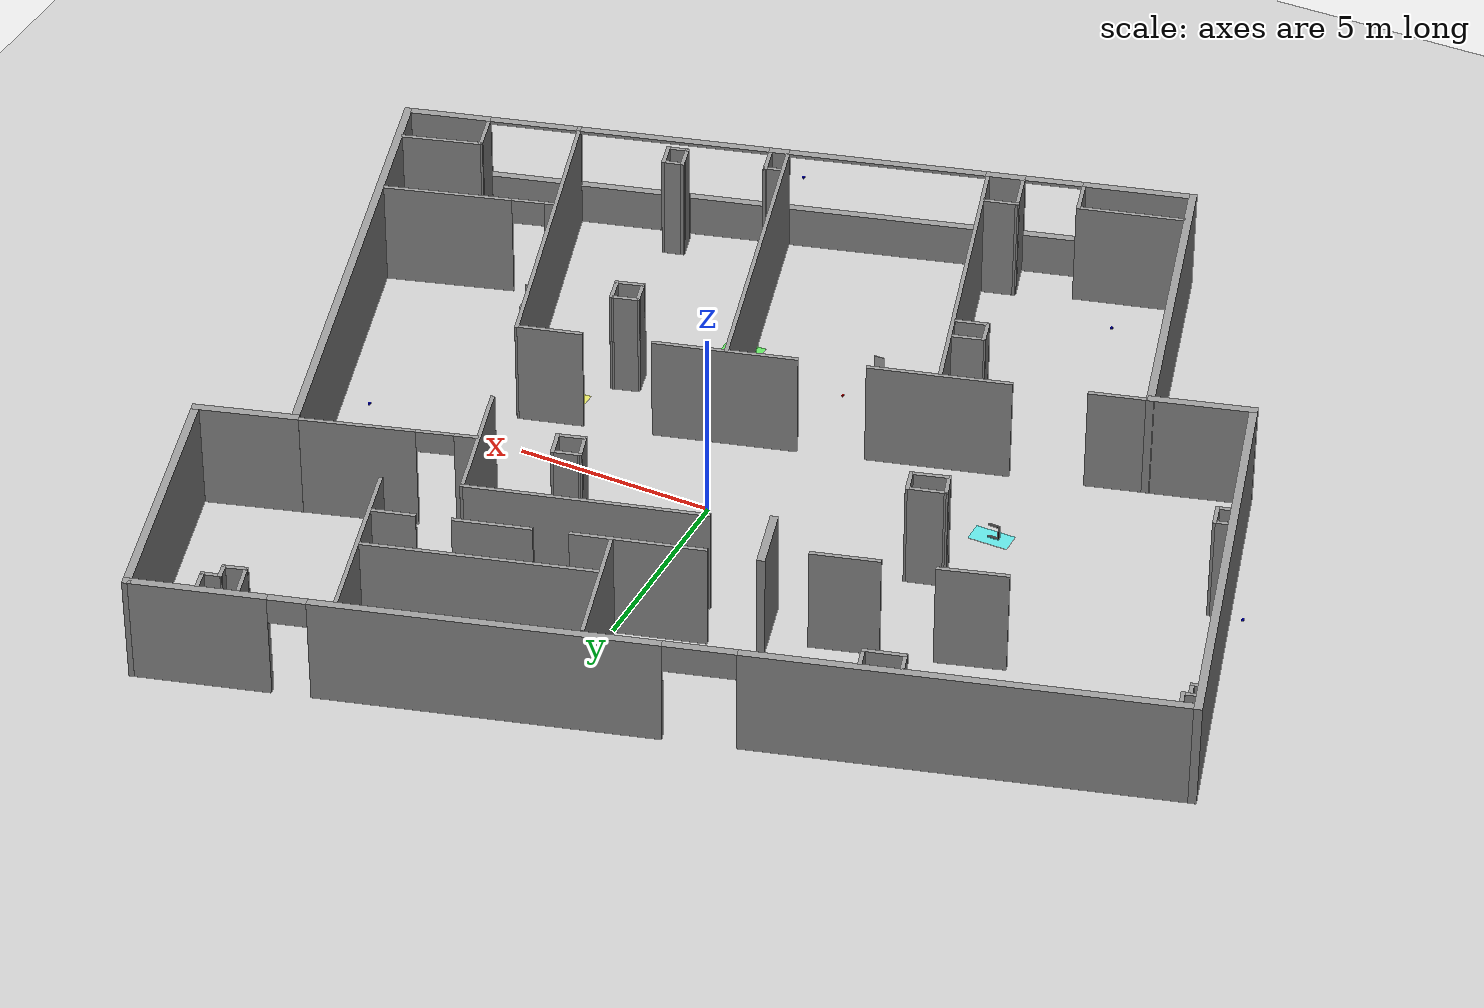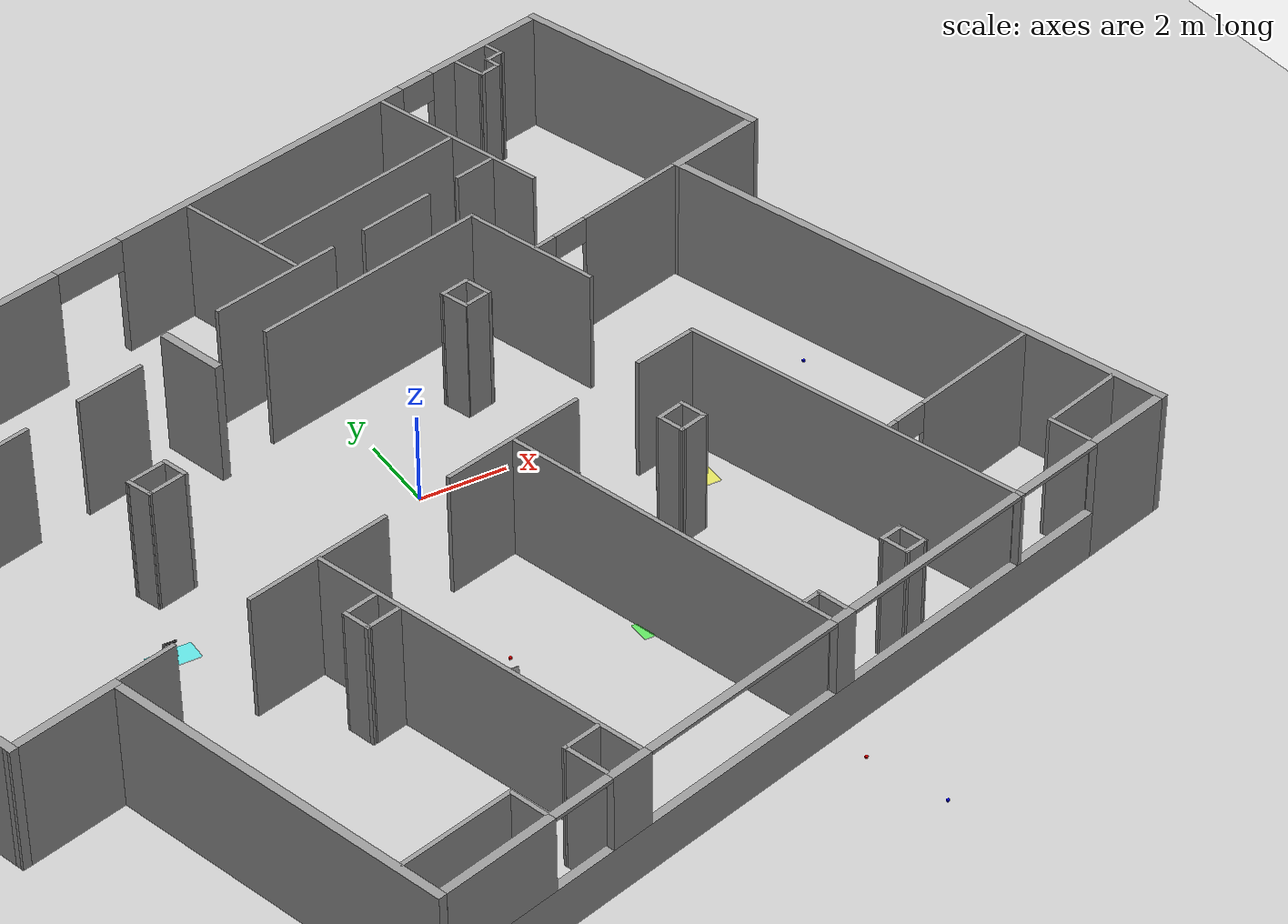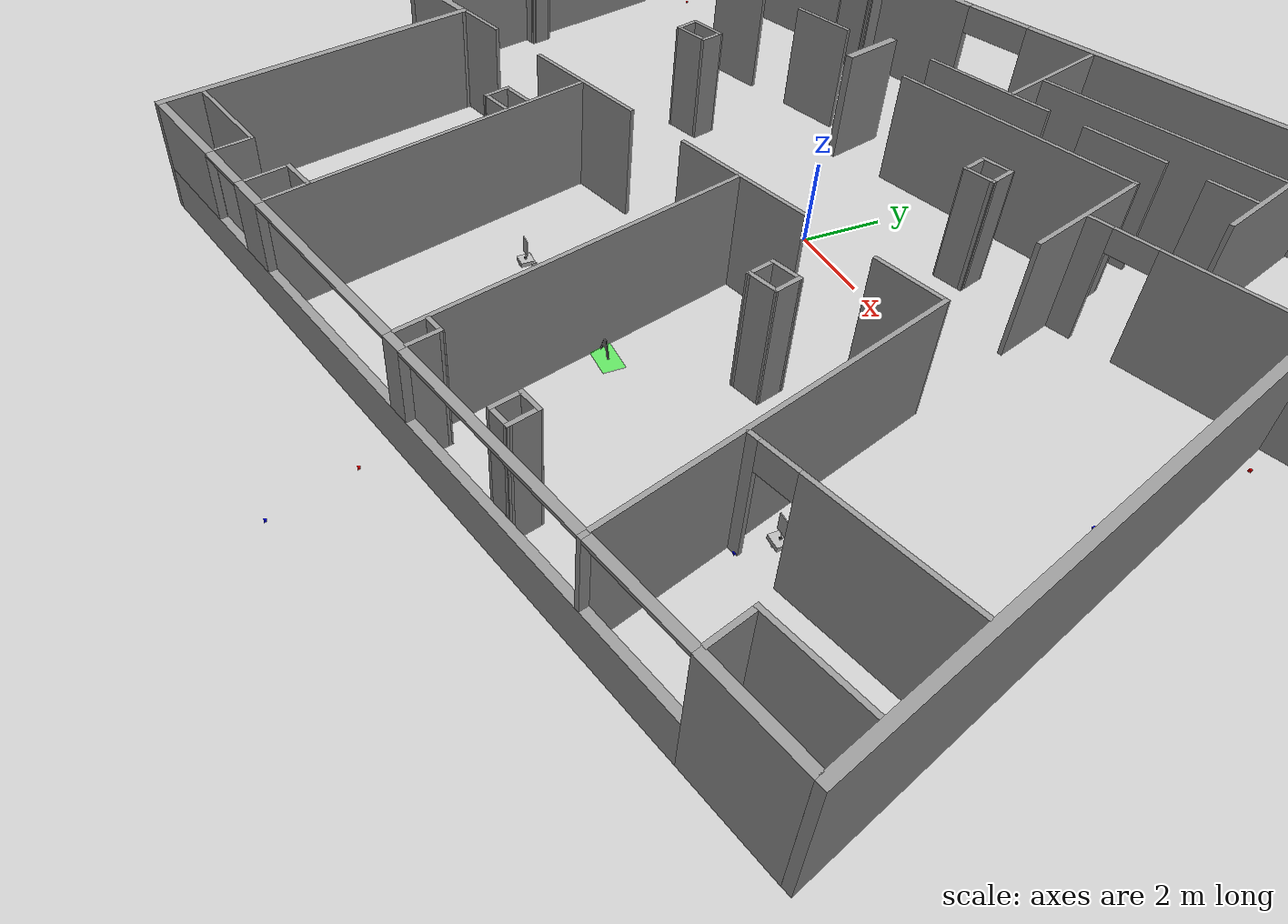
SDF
<?xml version='1.0' encoding='utf-8'?>
<sdf version="1.7">
  <world name="default">
    <plugin name="gazebo_ros_state" filename="libgazebo_ros_state.so">
      <ros>
        <namespace>/demo</namespace>
        <remapping>model_states:=model_states_demo</remapping>
        <remapping>link_states:=link_states_demo</remapping>
      </ros>
      <update_rate>20.0</update_rate>
    </plugin>
    <light name="sun" type="directional">
      <cast_shadows>1</cast_shadows>
      <pose>0 0 10 0 -0 0</pose>
      <diffuse>0.8 0.8 0.8 1</diffuse>
      <specular>0.2 0.2 0.2 1</specular>
      <attenuation>
        <range>1000</range>
        <constant>0.9</constant>
        <linear>0.01</linear>
        <quadratic>0.001</quadratic>
      </attenuation>
      <direction>-0.5 0.1 -0.9</direction>
      <spot>
        <inner_angle>0</inner_angle>
        <outer_angle>0</outer_angle>
        <falloff>0</falloff>
      </spot>
    </light>
    <model name="ground_plane">
      <static>1</static>
      <link name="link">
        <collision name="collision">
          <geometry>
            <plane>
              <normal>0 0 1</normal>
              <size>100 100</size>
            </plane>
          </geometry>
          <surface>
            <friction>
              <ode>
                <mu>100</mu>
                <mu2>100</mu2>
              </ode>
              <torsional>
                <ode />
              </torsional>
            </friction>
            <bounce />
            <contact>
              <ode />
            </contact>
          </surface>
          <max_contacts>10</max_contacts>
        </collision>
        <visual name="visual">
          <cast_shadows>0</cast_shadows>
          <geometry>
            <plane>
              <normal>0 0 1</normal>
              <size>100 100</size>
            </plane>
          </geometry>
          <material>
            <script>
              <uri>file://media/materials/scripts/gazebo.material</uri>
              <name>Gazebo/Grey</name>
            </script>
          </material>
        </visual>
        <velocity_decay>
          <linear>0</linear>
          <angular>0</angular>
        </velocity_decay>
        <self_collide>0</self_collide>
        <kinematic>0</kinematic>
        <gravity>1</gravity>
        <enable_wind>0</enable_wind>
      </link>
    </model>
    <physics type="ode">
      <ode>
        <solver>
          <type>quick</type>
          <iters>20</iters>
          <sor>1</sor>
          <use_dynamic_moi_rescaling>0</use_dynamic_moi_rescaling>
        </solver>
        <constraints>
          <cfm>0</cfm>
          <erp>0.2</erp>
          <contact_max_correcting_vel>100</contact_max_correcting_vel>
          <contact_surface_layer>0</contact_surface_layer>
        </constraints>
      </ode>
      <real_time_update_rate>500</real_time_update_rate>
      <max_step_size>.002</max_step_size>
      <real_time_factor>1</real_time_factor>
      <max_contacts>20</max_contacts>
    </physics>
    <scene>
      <ambient>0.4 0.4 0.4 1</ambient>
      <background>0.7 0.7 0.7 1</background>
      <shadows>1</shadows>
    </scene>
    <spherical_coordinates>
      <surface_model>EARTH_WGS84</surface_model>
      <latitude_deg>0</latitude_deg>
      <longitude_deg>0</longitude_deg>
      <elevation>0</elevation>
      <heading_deg>0</heading_deg>
    </spherical_coordinates>
    <model name="PAL_office">
      <pose>-1 -1 0 0 -0 0</pose>
      <link name="Wall_10">
        <collision name="Wall_10_Collision">
          <geometry>
            <box>
              <size>6.73478 0.2 2.78</size>
            </box>
          </geometry>
          <pose>0 0 1.39 0 -0 0</pose>
          <max_contacts>10</max_contacts>
          <surface>
            <bounce />
            <friction>
              <ode />
              <torsional>
                <ode />
              </torsional>
            </friction>
            <contact>
              <ode />
            </contact>
          </surface>
        </collision>
        <visual name="Wall_10_Visual">
          <pose>0 0 1.39 0 -0 0</pose>
          <geometry>
            <box>
              <size>6.73478 0.2 2.78</size>
            </box>
          </geometry>
          <material>
            <script>
              <uri>file://media/materials/scripts/gazebo.material</uri>
              <name>Gazebo/Grey</name>
            </script>
            <ambient>0.5 0.5 0.5 1</ambient>
          </material>
        </visual>
        <pose>11.1005 9.10601 0 0 -0 1.85624</pose>
        <velocity_decay>
          <linear>0</linear>
          <angular>0</angular>
        </velocity_decay>
        <self_collide>0</self_collide>
        <kinematic>0</kinematic>
        <gravity>1</gravity>
        <enable_wind>0</enable_wind>
      </link>
      <link name="Wall_101">
        <collision name="Wall_101_Collision">
          <geometry>
            <box>
              <size>0.35 0.1 2.78</size>
            </box>
          </geometry>
          <pose>0 0 1.39 0 -0 0</pose>
          <max_contacts>10</max_contacts>
          <surface>
            <bounce />
            <friction>
              <ode />
              <torsional>
                <ode />
              </torsional>
            </friction>
            <contact>
              <ode />
            </contact>
          </surface>
        </collision>
        <visual name="Wall_101_Visual">
          <pose>0 0 1.39 0 -0 0</pose>
          <geometry>
            <box>
              <size>0.35 0.1 2.78</size>
            </box>
          </geometry>
          <material>
            <script>
              <uri>file://media/materials/scripts/gazebo.material</uri>
              <name>Gazebo/Grey</name>
            </script>
            <ambient>0.5 0.5 0.5 1</ambient>
          </material>
        </visual>
        <pose>-13.001 5.22701 0 0 0 -2.87429</pose>
        <velocity_decay>
          <linear>0</linear>
          <angular>0</angular>
        </velocity_decay>
        <self_collide>0</self_collide>
        <kinematic>0</kinematic>
        <gravity>1</gravity>
        <enable_wind>0</enable_wind>
      </link>
      <link name="Wall_103">
        <collision name="Wall_103_Collision">
          <geometry>
            <box>
              <size>0.35 0.1 2.78</size>
            </box>
          </geometry>
          <pose>0 0 1.39 0 -0 0</pose>
          <max_contacts>10</max_contacts>
          <surface>
            <bounce />
            <friction>
              <ode />
              <torsional>
                <ode />
              </torsional>
            </friction>
            <contact>
              <ode />
            </contact>
          </surface>
        </collision>
        <visual name="Wall_103_Visual">
          <pose>0 0 1.39 0 -0 0</pose>
          <geometry>
            <box>
              <size>0.35 0.1 2.78</size>
            </box>
          </geometry>
          <material>
            <script>
              <uri>file://media/materials/scripts/gazebo.material</uri>
              <name>Gazebo/Grey</name>
            </script>
            <ambient>0.5 0.5 0.5 1</ambient>
          </material>
        </visual>
        <pose>-12.915 5.38001 0 0 -0 1.85075</pose>
        <velocity_decay>
          <linear>0</linear>
          <angular>0</angular>
        </velocity_decay>
        <self_collide>0</self_collide>
        <kinematic>0</kinematic>
        <gravity>1</gravity>
        <enable_wind>0</enable_wind>
      </link>
      <link name="Wall_113">
        <collision name="Wall_113_Collision">
          <geometry>
            <box>
              <size>0.183 0.1 2.78</size>
            </box>
          </geometry>
          <pose>0 0 1.39 0 -0 0</pose>
          <max_contacts>10</max_contacts>
          <surface>
            <bounce />
            <friction>
              <ode />
              <torsional>
                <ode />
              </torsional>
            </friction>
            <contact>
              <ode />
            </contact>
          </surface>
        </collision>
        <visual name="Wall_113_Visual">
          <pose>0 0 1.39 0 -0 0</pose>
          <geometry>
            <box>
              <size>0.183 0.1 2.78</size>
            </box>
          </geometry>
          <material>
            <script>
              <uri>file://media/materials/scripts/gazebo.material</uri>
              <name>Gazebo/Grey</name>
            </script>
            <ambient>0.5 0.5 0.5 1</ambient>
          </material>
        </visual>
        <pose>-12.9885 4.88001 0 0 -0 0.268366</pose>
        <velocity_decay>
          <linear>0</linear>
          <angular>0</angular>
        </velocity_decay>
        <self_collide>0</self_collide>
        <kinematic>0</kinematic>
        <gravity>1</gravity>
        <enable_wind>0</enable_wind>
      </link>
      <link name="Wall_118">
        <collision name="Wall_118_Collision">
          <geometry>
            <box>
              <size>0.252054 0.1 2.78</size>
            </box>
          </geometry>
          <pose>0 0 1.39 0 -0 0</pose>
          <max_contacts>10</max_contacts>
          <surface>
            <bounce />
            <friction>
              <ode />
              <torsional>
                <ode />
              </torsional>
            </friction>
            <contact>
              <ode />
            </contact>
          </surface>
        </collision>
        <visual name="Wall_118_Visual">
          <pose>0 0 1.39 0 -0 0</pose>
          <geometry>
            <box>
              <size>0.252054 0.1 2.78</size>
            </box>
          </geometry>
          <material>
            <script>
              <uri>file://media/materials/scripts/gazebo.material</uri>
              <name>Gazebo/Grey</name>
            </script>
            <ambient>0.5 0.5 0.5 1</ambient>
          </material>
        </visual>
        <pose>-12.996 5.05551 0 0 0 -1.31147</pose>
        <velocity_decay>
          <linear>0</linear>
          <angular>0</angular>
        </velocity_decay>
        <self_collide>0</self_collide>
        <kinematic>0</kinematic>
        <gravity>1</gravity>
        <enable_wind>0</enable_wind>
      </link>
      <link name="Wall_12">
        <collision name="Wall_12_Collision">
          <geometry>
            <box>
              <size>2.648 0.2 2.78</size>
            </box>
          </geometry>
          <pose>0 0 1.39 0 -0 0</pose>
          <max_contacts>10</max_contacts>
          <surface>
            <bounce />
            <friction>
              <ode />
              <torsional>
                <ode />
              </torsional>
            </friction>
            <contact>
              <ode />
            </contact>
          </surface>
        </collision>
        <visual name="Wall_12_Visual">
          <pose>0 0 1.39 0 -0 0</pose>
          <geometry>
            <box>
              <size>2.648 0.2 2.78</size>
            </box>
          </geometry>
          <material>
            <script>
              <uri>file://media/materials/scripts/gazebo.material</uri>
              <name>Gazebo/Grey</name>
            </script>
            <ambient>0.5 0.5 0.5 1</ambient>
          </material>
        </visual>
        <pose>-9.23199 -4.61199 0 0 0 -2.8652</pose>
        <velocity_decay>
          <linear>0</linear>
          <angular>0</angular>
        </velocity_decay>
        <self_collide>0</self_collide>
        <kinematic>0</kinematic>
        <gravity>1</gravity>
        <enable_wind>0</enable_wind>
      </link>
      <link name="Wall_121">
        <collision name="Wall_121_Collision">
          <geometry>
            <box>
              <size>1.01214 0.1 2.78</size>
            </box>
          </geometry>
          <pose>0 0 1.39 0 -0 0</pose>
          <max_contacts>10</max_contacts>
          <surface>
            <bounce />
            <friction>
              <ode />
              <torsional>
                <ode />
              </torsional>
            </friction>
            <contact>
              <ode />
            </contact>
          </surface>
        </collision>
        <visual name="Wall_121_Visual">
          <pose>0 0 1.39 0 -0 0</pose>
          <geometry>
            <box>
              <size>1.01214 0.1 2.78</size>
            </box>
          </geometry>
          <material>
            <script>
              <uri>file://media/materials/scripts/gazebo.material</uri>
              <name>Gazebo/Grey</name>
            </script>
            <ambient>0.5 0.5 0.5 1</ambient>
          </material>
        </visual>
        <pose>-4.76149 1.21201 0 0 -0 0.266252</pose>
        <velocity_decay>
          <linear>0</linear>
          <angular>0</angular>
        </velocity_decay>
        <self_collide>0</self_collide>
        <kinematic>0</kinematic>
        <gravity>1</gravity>
        <enable_wind>0</enable_wind>
      </link>
      <link name="Wall_122">
        <collision name="Wall_122_Collision">
          <geometry>
            <box>
              <size>0.660446 0.1 2.78</size>
            </box>
          </geometry>
          <pose>0 0 1.39 0 -0 0</pose>
          <max_contacts>10</max_contacts>
          <surface>
            <bounce />
            <friction>
              <ode />
              <torsional>
                <ode />
              </torsional>
            </friction>
            <contact>
              <ode />
            </contact>
          </surface>
        </collision>
        <visual name="Wall_122_Visual">
          <pose>0 0 1.39 0 -0 0</pose>
          <geometry>
            <box>
              <size>0.660446 0.1 2.78</size>
            </box>
          </geometry>
          <material>
            <script>
              <uri>file://media/materials/scripts/gazebo.material</uri>
              <name>Gazebo/Grey</name>
            </script>
            <ambient>0.5 0.5 0.5 1</ambient>
          </material>
        </visual>
        <pose>-4.24649 1.06201 0 0 0 -1.29985</pose>
        <velocity_decay>
          <linear>0</linear>
          <angular>0</angular>
        </velocity_decay>
        <self_collide>0</self_collide>
        <kinematic>0</kinematic>
        <gravity>1</gravity>
        <enable_wind>0</enable_wind>
      </link>
      <link name="Wall_127">
        <collision name="Wall_127_Collision">
          <geometry>
            <box>
              <size>0.678705 0.1 2.78</size>
            </box>
          </geometry>
          <pose>0 0 1.39 0 -0 0</pose>
          <max_contacts>10</max_contacts>
          <surface>
            <bounce />
            <friction>
              <ode />
              <torsional>
                <ode />
              </torsional>
            </friction>
            <contact>
              <ode />
            </contact>
          </surface>
        </collision>
        <visual name="Wall_127_Visual">
          <pose>0 0 1.39 0 -0 0</pose>
          <geometry>
            <box>
              <size>0.678705 0.1 2.78</size>
            </box>
          </geometry>
          <material>
            <script>
              <uri>file://media/materials/scripts/gazebo.material</uri>
              <name>Gazebo/Grey</name>
            </script>
            <ambient>0.5 0.5 0.5 1</ambient>
          </material>
        </visual>
        <pose>-5.11149 0.817011 0 0 0 -1.25451</pose>
        <velocity_decay>
          <linear>0</linear>
          <angular>0</angular>
        </velocity_decay>
        <self_collide>0</self_collide>
        <kinematic>0</kinematic>
        <gravity>1</gravity>
        <enable_wind>0</enable_wind>
      </link>
      <link name="Wall_128">
        <collision name="Wall_128_Collision">
          <geometry>
            <box>
              <size>0.913204 0.1 2.78</size>
            </box>
          </geometry>
          <pose>0 0 1.39 0 -0 0</pose>
          <max_contacts>10</max_contacts>
          <surface>
            <bounce />
            <friction>
              <ode />
              <torsional>
                <ode />
              </torsional>
            </friction>
            <contact>
              <ode />
            </contact>
          </surface>
        </collision>
        <visual name="Wall_128_Visual">
          <pose>0 0 1.39 0 -0 0</pose>
          <geometry>
            <box>
              <size>0.913204 0.1 2.78</size>
            </box>
          </geometry>
          <material>
            <script>
              <uri>file://media/materials/scripts/gazebo.material</uri>
              <name>Gazebo/Grey</name>
            </script>
            <ambient>0.5 0.5 0.5 1</ambient>
          </material>
        </visual>
        <pose>-4.63149 0.657011 0 0 -0 0.286745</pose>
        <velocity_decay>
          <linear>0</linear>
          <angular>0</angular>
        </velocity_decay>
        <self_collide>0</self_collide>
        <kinematic>0</kinematic>
        <gravity>1</gravity>
        <enable_wind>0</enable_wind>
      </link>
      <link name="Wall_133">
        <collision name="Wall_133_Collision">
          <geometry>
            <box>
              <size>0.754498 0.1 2.78</size>
            </box>
          </geometry>
          <pose>0 0 1.39 0 -0 0</pose>
          <max_contacts>10</max_contacts>
          <surface>
            <bounce />
            <friction>
              <ode />
              <torsional>
                <ode />
              </torsional>
            </friction>
            <contact>
              <ode />
            </contact>
          </surface>
        </collision>
        <visual name="Wall_133_Visual">
          <pose>0 0 1.39 0 -0 0</pose>
          <geometry>
            <box>
              <size>0.754498 0.1 2.78</size>
            </box>
          </geometry>
          <material>
            <script>
              <uri>file://media/materials/scripts/gazebo.material</uri>
              <name>Gazebo/Grey</name>
            </script>
            <ambient>0.5 0.5 0.5 1</ambient>
          </material>
        </visual>
        <pose>3.37451 3.66401 0 0 -0 0.275362</pose>
        <velocity_decay>
          <linear>0</linear>
          <angular>0</angular>
        </velocity_decay>
        <self_collide>0</self_collide>
        <kinematic>0</kinematic>
        <gravity>1</gravity>
        <enable_wind>0</enable_wind>
      </link>
      <link name="Wall_134">
        <collision name="Wall_134_Collision">
          <geometry>
            <box>
              <size>0.726947 0.1 2.78</size>
            </box>
          </geometry>
          <pose>0 0 1.39 0 -0 0</pose>
          <max_contacts>10</max_contacts>
          <surface>
            <bounce />
            <friction>
              <ode />
              <torsional>
                <ode />
              </torsional>
            </friction>
            <contact>
              <ode />
            </contact>
          </surface>
        </collision>
        <visual name="Wall_134_Visual">
          <pose>0 0 1.39 0 -0 0</pose>
          <geometry>
            <box>
              <size>0.726947 0.1 2.78</size>
            </box>
          </geometry>
          <material>
            <script>
              <uri>file://media/materials/scripts/gazebo.material</uri>
              <name>Gazebo/Grey</name>
            </script>
            <ambient>0.5 0.5 0.5 1</ambient>
          </material>
        </visual>
        <pose>3.77951 3.45301 0 0 0 -1.27934</pose>
        <velocity_decay>
          <linear>0</linear>
          <angular>0</angular>
        </velocity_decay>
        <self_collide>0</self_collide>
        <kinematic>0</kinematic>
        <gravity>1</gravity>
        <enable_wind>0</enable_wind>
      </link>
      <link name="Wall_14">
        <collision name="Wall_14_Collision">
          <geometry>
            <box>
              <size>8.475 0.2 2.78</size>
            </box>
          </geometry>
          <pose>0 0 1.39 0 -0 0</pose>
          <max_contacts>10</max_contacts>
          <surface>
            <bounce />
            <friction>
              <ode />
              <torsional>
                <ode />
              </torsional>
            </friction>
            <contact>
              <ode />
            </contact>
          </surface>
        </collision>
        <visual name="Wall_14_Visual">
          <pose>0 0 1.39 0 -0 0</pose>
          <geometry>
            <box>
              <size>8.475 0.2 2.78</size>
            </box>
          </geometry>
          <material>
            <script>
              <uri>file://media/materials/scripts/gazebo.material</uri>
              <name>Gazebo/Grey</name>
            </script>
            <ambient>0.5 0.5 0.5 1</ambient>
          </material>
        </visual>
        <pose>-6.93049 -8.25999 0 0 0 -1.29568</pose>
        <velocity_decay>
          <linear>0</linear>
          <angular>0</angular>
        </velocity_decay>
        <self_collide>0</self_collide>
        <kinematic>0</kinematic>
        <gravity>1</gravity>
        <enable_wind>0</enable_wind>
      </link>
      <link name="Wall_140">
        <collision name="Wall_140_Collision">
          <geometry>
            <box>
              <size>0.729033 0.1 2.78</size>
            </box>
          </geometry>
          <pose>0 0 1.39 0 -0 0</pose>
          <max_contacts>10</max_contacts>
          <surface>
            <bounce />
            <friction>
              <ode />
              <torsional>
                <ode />
              </torsional>
            </friction>
            <contact>
              <ode />
            </contact>
          </surface>
        </collision>
        <visual name="Wall_140_Visual">
          <pose>0 0 1.39 0 -0 0</pose>
          <geometry>
            <box>
              <size>0.729033 0.1 2.78</size>
            </box>
          </geometry>
          <material>
            <script>
              <uri>file://media/materials/scripts/gazebo.material</uri>
              <name>Gazebo/Grey</name>
            </script>
            <ambient>0.5 0.5 0.5 1</ambient>
          </material>
        </visual>
        <pose>3.15251 3.27451 0 0 0 -1.27066</pose>
        <velocity_decay>
          <linear>0</linear>
          <angular>0</angular>
        </velocity_decay>
        <self_collide>0</self_collide>
        <kinematic>0</kinematic>
        <gravity>1</gravity>
        <enable_wind>0</enable_wind>
      </link>
      <link name="Wall_142">
        <collision name="Wall_142_Collision">
          <geometry>
            <box>
              <size>0.721105 0.1 2.78</size>
            </box>
          </geometry>
          <pose>0 0 1.39 0 -0 0</pose>
          <max_contacts>10</max_contacts>
          <surface>
            <bounce />
            <friction>
              <ode />
              <torsional>
                <ode />
              </torsional>
            </friction>
            <contact>
              <ode />
            </contact>
          </surface>
        </collision>
        <visual name="Wall_142_Visual">
          <pose>0 0 1.39 0 -0 0</pose>
          <geometry>
            <box>
              <size>0.721105 0.1 2.78</size>
            </box>
          </geometry>
          <material>
            <script>
              <uri>file://media/materials/scripts/gazebo.material</uri>
              <name>Gazebo/Grey</name>
            </script>
            <ambient>0.5 0.5 0.5 1</ambient>
          </material>
        </visual>
        <pose>3.57151 3.06601 0 0 0 -2.85754</pose>
        <velocity_decay>
          <linear>0</linear>
          <angular>0</angular>
        </velocity_decay>
        <self_collide>0</self_collide>
        <kinematic>0</kinematic>
        <gravity>1</gravity>
        <enable_wind>0</enable_wind>
      </link>
      <link name="Wall_145">
        <collision name="Wall_145_Collision">
          <geometry>
            <box>
              <size>8.27375 0.1 2.78</size>
            </box>
          </geometry>
          <pose>0 0 1.39 0 -0 0</pose>
          <max_contacts>10</max_contacts>
          <surface>
            <bounce />
            <friction>
              <ode />
              <torsional>
                <ode />
              </torsional>
            </friction>
            <contact>
              <ode />
            </contact>
          </surface>
        </collision>
        <visual name="Wall_145_Visual">
          <pose>0 0 1.39 0 -0 0</pose>
          <geometry>
            <box>
              <size>8.27375 0.1 2.78</size>
            </box>
          </geometry>
          <material>
            <script>
              <uri>file://media/materials/scripts/gazebo.material</uri>
              <name>Gazebo/Grey</name>
            </script>
            <ambient>0.5 0.5 0.5 1</ambient>
          </material>
        </visual>
        <pose>7.88901 -4.08549 0 0 0 -1.27598</pose>
        <velocity_decay>
          <linear>0</linear>
          <angular>0</angular>
        </velocity_decay>
        <self_collide>0</self_collide>
        <kinematic>0</kinematic>
        <gravity>1</gravity>
        <enable_wind>0</enable_wind>
      </link>
      <link name="Wall_147">
        <collision name="Wall_147_Collision">
          <geometry>
            <box>
              <size>1.6624 0.1 2.78</size>
            </box>
          </geometry>
          <pose>0 0 1.39 0 -0 0</pose>
          <max_contacts>10</max_contacts>
          <surface>
            <bounce />
            <friction>
              <ode />
              <torsional>
                <ode />
              </torsional>
            </friction>
            <contact>
              <ode />
            </contact>
          </surface>
        </collision>
        <visual name="Wall_147_Visual">
          <pose>0 0 1.39 0 -0 0</pose>
          <geometry>
            <box>
              <size>1.6624 0.1 2.78</size>
            </box>
          </geometry>
          <material>
            <script>
              <uri>file://media/materials/scripts/gazebo.material</uri>
              <name>Gazebo/Grey</name>
            </script>
            <ambient>0.5 0.5 0.5 1</ambient>
          </material>
        </visual>
        <pose>5.94751 -0.379989 0 0 0 -2.87613</pose>
        <velocity_decay>
          <linear>0</linear>
          <angular>0</angular>
        </velocity_decay>
        <self_collide>0</self_collide>
        <kinematic>0</kinematic>
        <gravity>1</gravity>
        <enable_wind>0</enable_wind>
      </link>
      <link name="Wall_150">
        <pose>10.26 -4.39249 0 0 -0 0.289894</pose>
        <visual name="Wall_150_Visual_0">
          <pose>-2.03127 0 1.39 0 -0 0</pose>
          <geometry>
            <box>
              <size>0.2671 0.1 2.78</size>
            </box>
          </geometry>
          <material>
            <script>
              <uri>file://media/materials/scripts/gazebo.material</uri>
              <name>Gazebo/Grey</name>
            </script>
            <ambient>0.5 0.5 0.5 1</ambient>
          </material>
        </visual>
        <collision name="Wall_150_Collision_0">
          <geometry>
            <box>
              <size>0.2671 0.1 2.78</size>
            </box>
          </geometry>
          <pose>-2.03127 0 1.39 0 -0 0</pose>
          <max_contacts>10</max_contacts>
          <surface>
            <bounce />
            <friction>
              <ode />
              <torsional>
                <ode />
              </torsional>
            </friction>
            <contact>
              <ode />
            </contact>
          </surface>
        </collision>
        <visual name="Wall_150_Visual_1">
          <pose>0.54355 0 1.39 0 -0 0</pose>
          <geometry>
            <box>
              <size>3.24255 0.1 2.78</size>
            </box>
          </geometry>
          <material>
            <script>
              <uri>file://media/materials/scripts/gazebo.material</uri>
              <name>Gazebo/Grey</name>
            </script>
            <ambient>0.5 0.5 0.5 1</ambient>
          </material>
        </visual>
        <collision name="Wall_150_Collision_1">
          <geometry>
            <box>
              <size>3.24255 0.1 2.78</size>
            </box>
          </geometry>
          <pose>0.54355 0 1.39 0 -0 0</pose>
          <max_contacts>10</max_contacts>
          <surface>
            <bounce />
            <friction>
              <ode />
              <torsional>
                <ode />
              </torsional>
            </friction>
            <contact>
              <ode />
            </contact>
          </surface>
        </collision>
        <visual name="Wall_150_Visual_2">
          <pose>-1.48772 0 2.44 0 -0 0</pose>
          <geometry>
            <box>
              <size>0.82 0.1 0.68</size>
            </box>
          </geometry>
          <material>
            <script>
              <uri>file://media/materials/scripts/gazebo.material</uri>
              <name>Gazebo/Grey</name>
            </script>
            <ambient>0.5 0.5 0.5 1</ambient>
          </material>
        </visual>
        <collision name="Wall_150_Collision_2">
          <geometry>
            <box>
              <size>0.82 0.1 0.68</size>
            </box>
          </geometry>
          <pose>-1.48772 0 2.44 0 -0 0</pose>
          <max_contacts>10</max_contacts>
          <surface>
            <bounce />
            <friction>
              <ode />
              <torsional>
                <ode />
              </torsional>
            </friction>
            <contact>
              <ode />
            </contact>
          </surface>
        </collision>
        <velocity_decay>
          <linear>0</linear>
          <angular>0</angular>
        </velocity_decay>
        <self_collide>0</self_collide>
        <kinematic>0</kinematic>
        <gravity>1</gravity>
        <enable_wind>0</enable_wind>
      </link>
      <link name="Wall_153">
        <collision name="Wall_153_Collision">
          <geometry>
            <box>
              <size>2.08407 0.1 2.78</size>
            </box>
          </geometry>
          <pose>0 0 1.39 0 -0 0</pose>
          <max_contacts>10</max_contacts>
          <surface>
            <bounce />
            <friction>
              <ode />
              <torsional>
                <ode />
              </torsional>
            </friction>
            <contact>
              <ode />
            </contact>
          </surface>
        </collision>
        <visual name="Wall_153_Visual">
          <pose>0 0 1.39 0 -0 0</pose>
          <geometry>
            <box>
              <size>2.08407 0.1 2.78</size>
            </box>
          </geometry>
          <material>
            <script>
              <uri>file://media/materials/scripts/gazebo.material</uri>
              <name>Gazebo/Grey</name>
            </script>
            <ambient>0.5 0.5 0.5 1</ambient>
          </material>
        </visual>
        <pose>11.9955 -6.18599 0 0 0 -2.85014</pose>
        <velocity_decay>
          <linear>0</linear>
          <angular>0</angular>
        </velocity_decay>
        <self_collide>0</self_collide>
        <kinematic>0</kinematic>
        <gravity>1</gravity>
        <enable_wind>0</enable_wind>
      </link>
      <link name="Wall_154">
        <collision name="Wall_154_Collision">
          <geometry>
            <box>
              <size>1.04397 0.1 2.78</size>
            </box>
          </geometry>
          <pose>0 0 1.39 0 -0 0</pose>
          <max_contacts>10</max_contacts>
          <surface>
            <bounce />
            <friction>
              <ode />
              <torsional>
                <ode />
              </torsional>
            </friction>
            <contact>
              <ode />
            </contact>
          </surface>
        </collision>
        <visual name="Wall_154_Visual">
          <pose>0 0 1.39 0 -0 0</pose>
          <geometry>
            <box>
              <size>1.04397 0.1 2.78</size>
            </box>
          </geometry>
          <material>
            <script>
              <uri>file://media/materials/scripts/gazebo.material</uri>
              <name>Gazebo/Grey</name>
            </script>
            <ambient>0.5 0.5 0.5 1</ambient>
          </material>
        </visual>
        <pose>11.176 -6.92449 0 0 0 -1.29061</pose>
        <velocity_decay>
          <linear>0</linear>
          <angular>0</angular>
        </velocity_decay>
        <self_collide>0</self_collide>
        <kinematic>0</kinematic>
        <gravity>1</gravity>
        <enable_wind>0</enable_wind>
      </link>
      <link name="Wall_158">
        <collision name="Wall_158_Collision">
          <geometry>
            <box>
              <size>3.52366 0.1 2.78</size>
            </box>
          </geometry>
          <pose>0 0 1.39 0 -0 0</pose>
          <max_contacts>10</max_contacts>
          <surface>
            <bounce />
            <friction>
              <ode />
              <torsional>
                <ode />
              </torsional>
            </friction>
            <contact>
              <ode />
            </contact>
          </surface>
        </collision>
        <visual name="Wall_158_Visual">
          <pose>0 0 1.39 0 -0 0</pose>
          <geometry>
            <box>
              <size>3.52366 0.1 2.78</size>
            </box>
          </geometry>
          <material>
            <script>
              <uri>file://media/materials/scripts/gazebo.material</uri>
              <name>Gazebo/Grey</name>
            </script>
            <ambient>0.5 0.5 0.5 1</ambient>
          </material>
        </visual>
        <pose>-3.20649 -2.89249 0 0 -0 0.269352</pose>
        <velocity_decay>
          <linear>0</linear>
          <angular>0</angular>
        </velocity_decay>
        <self_collide>0</self_collide>
        <kinematic>0</kinematic>
        <gravity>1</gravity>
        <enable_wind>0</enable_wind>
      </link>
      <link name="Wall_16">
        <pose>3.78351 -9.59399 0 0 0 -2.87199</pose>
        <visual name="Wall_16_Visual_0">
          <pose>-8.83974 0 1.39 0 -0 0</pose>
          <geometry>
            <box>
              <size>2.04382 0.2 2.78</size>
            </box>
          </geometry>
          <material>
            <script>
              <uri>file://media/materials/scripts/gazebo.material</uri>
              <name>Gazebo/Grey</name>
            </script>
            <ambient>0.5 0.5 0.5 1</ambient>
          </material>
        </visual>
        <collision name="Wall_16_Collision_0">
          <geometry>
            <box>
              <size>2.04382 0.2 2.78</size>
            </box>
          </geometry>
          <pose>-8.83974 0 1.39 0 -0 0</pose>
          <max_contacts>10</max_contacts>
          <surface>
            <bounce />
            <friction>
              <ode />
              <torsional>
                <ode />
              </torsional>
            </friction>
            <contact>
              <ode />
            </contact>
          </surface>
        </collision>
        <visual name="Wall_16_Visual_1">
          <pose>1.02191 0 0.55 0 -0 0</pose>
          <geometry>
            <box>
              <size>17.6795 0.2 1.1</size>
            </box>
          </geometry>
          <material>
            <script>
              <uri>file://media/materials/scripts/gazebo.material</uri>
              <name>Gazebo/Grey</name>
            </script>
            <ambient>0.5 0.5 0.5 1</ambient>
          </material>
        </visual>
        <collision name="Wall_16_Collision_1">
          <geometry>
            <box>
              <size>17.6795 0.2 1.1</size>
            </box>
          </geometry>
          <pose>1.02191 0 0.55 0 -0 0</pose>
          <max_contacts>10</max_contacts>
          <surface>
            <bounce />
            <friction>
              <ode />
              <torsional>
                <ode />
              </torsional>
            </friction>
            <contact>
              <ode />
            </contact>
          </surface>
        </collision>
        <visual name="Wall_16_Visual_2">
          <pose>-5.54535 0 1.94 0 -0 0</pose>
          <geometry>
            <box>
              <size>0.100368 0.2 1.68</size>
            </box>
          </geometry>
          <material>
            <script>
              <uri>file://media/materials/scripts/gazebo.material</uri>
              <name>Gazebo/Grey</name>
            </script>
            <ambient>0.5 0.5 0.5 1</ambient>
          </material>
        </visual>
        <collision name="Wall_16_Collision_2">
          <geometry>
            <box>
              <size>0.100368 0.2 1.68</size>
            </box>
          </geometry>
          <pose>-5.54535 0 1.94 0 -0 0</pose>
          <max_contacts>10</max_contacts>
          <surface>
            <bounce />
            <friction>
              <ode />
              <torsional>
                <ode />
              </torsional>
            </friction>
            <contact>
              <ode />
            </contact>
          </surface>
        </collision>
        <visual name="Wall_16_Visual_3">
          <pose>-0.435842 0 1.94 0 -0 0</pose>
          <geometry>
            <box>
              <size>0.509797 0.2 1.68</size>
            </box>
          </geometry>
          <material>
            <script>
              <uri>file://media/materials/scripts/gazebo.material</uri>
              <name>Gazebo/Grey</name>
            </script>
            <ambient>0.5 0.5 0.5 1</ambient>
          </material>
        </visual>
        <collision name="Wall_16_Collision_3">
          <geometry>
            <box>
              <size>0.509797 0.2 1.68</size>
            </box>
          </geometry>
          <pose>-0.435842 0 1.94 0 -0 0</pose>
          <max_contacts>10</max_contacts>
          <surface>
            <bounce />
            <friction>
              <ode />
              <torsional>
                <ode />
              </torsional>
            </friction>
            <contact>
              <ode />
            </contact>
          </surface>
        </collision>
        <visual name="Wall_16_Visual_4">
          <pose>5.27686 0 1.94 0 -0 0</pose>
          <geometry>
            <box>
              <size>0.994619 0.2 1.68</size>
            </box>
          </geometry>
          <material>
            <script>
              <uri>file://media/materials/scripts/gazebo.material</uri>
              <name>Gazebo/Grey</name>
            </script>
            <ambient>0.5 0.5 0.5 1</ambient>
          </material>
        </visual>
        <collision name="Wall_16_Collision_4">
          <geometry>
            <box>
              <size>0.994619 0.2 1.68</size>
            </box>
          </geometry>
          <pose>5.27686 0 1.94 0 -0 0</pose>
          <max_contacts>10</max_contacts>
          <surface>
            <bounce />
            <friction>
              <ode />
              <torsional>
                <ode />
              </torsional>
            </friction>
            <contact>
              <ode />
            </contact>
          </surface>
        </collision>
        <visual name="Wall_16_Visual_5">
          <pose>8.53741 0 1.94 0 -0 0</pose>
          <geometry>
            <box>
              <size>2.64848 0.2 1.68</size>
            </box>
          </geometry>
          <material>
            <script>
              <uri>file://media/materials/scripts/gazebo.material</uri>
              <name>Gazebo/Grey</name>
            </script>
            <ambient>0.5 0.5 0.5 1</ambient>
          </material>
        </visual>
        <collision name="Wall_16_Collision_5">
          <geometry>
            <box>
              <size>2.64848 0.2 1.68</size>
            </box>
          </geometry>
          <pose>8.53741 0 1.94 0 -0 0</pose>
          <max_contacts>10</max_contacts>
          <surface>
            <bounce />
            <friction>
              <ode />
              <torsional>
                <ode />
              </torsional>
            </friction>
            <contact>
              <ode />
            </contact>
          </surface>
        </collision>
        <visual name="Wall_16_Visual_6">
          <pose>-6.70668 0 2.74 0 -0 0</pose>
          <geometry>
            <box>
              <size>2.22229 0.2 0.08</size>
            </box>
          </geometry>
          <material>
            <script>
              <uri>file://media/materials/scripts/gazebo.material</uri>
              <name>Gazebo/Grey</name>
            </script>
            <ambient>0.5 0.5 0.5 1</ambient>
          </material>
        </visual>
        <collision name="Wall_16_Collision_6">
          <geometry>
            <box>
              <size>2.22229 0.2 0.08</size>
            </box>
          </geometry>
          <pose>-6.70668 0 2.74 0 -0 0</pose>
          <max_contacts>10</max_contacts>
          <surface>
            <bounce />
            <friction>
              <ode />
              <torsional>
                <ode />
              </torsional>
            </friction>
            <contact>
              <ode />
            </contact>
          </surface>
        </collision>
        <visual name="Wall_16_Visual_7">
          <pose>-3.09295 0 2.74 0 -0 0</pose>
          <geometry>
            <box>
              <size>4.80443 0.2 0.08</size>
            </box>
          </geometry>
          <material>
            <script>
              <uri>file://media/materials/scripts/gazebo.material</uri>
              <name>Gazebo/Grey</name>
            </script>
            <ambient>0.5 0.5 0.5 1</ambient>
          </material>
        </visual>
        <collision name="Wall_16_Collision_7">
          <geometry>
            <box>
              <size>4.80443 0.2 0.08</size>
            </box>
          </geometry>
          <pose>-3.09295 0 2.74 0 -0 0</pose>
          <max_contacts>10</max_contacts>
          <surface>
            <bounce />
            <friction>
              <ode />
              <torsional>
                <ode />
              </torsional>
            </friction>
            <contact>
              <ode />
            </contact>
          </surface>
        </collision>
        <visual name="Wall_16_Visual_8">
          <pose>2.2993 0 2.74 0 -0 0</pose>
          <geometry>
            <box>
              <size>4.96049 0.2 0.08</size>
            </box>
          </geometry>
          <material>
            <script>
              <uri>file://media/materials/scripts/gazebo.material</uri>
              <name>Gazebo/Grey</name>
            </script>
            <ambient>0.5 0.5 0.5 1</ambient>
          </material>
        </visual>
        <collision name="Wall_16_Collision_8">
          <geometry>
            <box>
              <size>4.96049 0.2 0.08</size>
            </box>
          </geometry>
          <pose>2.2993 0 2.74 0 -0 0</pose>
          <max_contacts>10</max_contacts>
          <surface>
            <bounce />
            <friction>
              <ode />
              <torsional>
                <ode />
              </torsional>
            </friction>
            <contact>
              <ode />
            </contact>
          </surface>
        </collision>
        <visual name="Wall_16_Visual_9">
          <pose>6.49367 0 2.74 0 -0 0</pose>
          <geometry>
            <box>
              <size>1.439 0.2 0.08</size>
            </box>
          </geometry>
          <material>
            <script>
              <uri>file://media/materials/scripts/gazebo.material</uri>
              <name>Gazebo/Grey</name>
            </script>
            <ambient>0.5 0.5 0.5 1</ambient>
          </material>
        </visual>
        <collision name="Wall_16_Collision_9">
          <geometry>
            <box>
              <size>1.439 0.2 0.08</size>
            </box>
          </geometry>
          <pose>6.49367 0 2.74 0 -0 0</pose>
          <max_contacts>10</max_contacts>
          <surface>
            <bounce />
            <friction>
              <ode />
              <torsional>
                <ode />
              </torsional>
            </friction>
            <contact>
              <ode />
            </contact>
          </surface>
        </collision>
        <velocity_decay>
          <linear>0</linear>
          <angular>0</angular>
        </velocity_decay>
        <self_collide>0</self_collide>
        <kinematic>0</kinematic>
        <gravity>1</gravity>
        <enable_wind>0</enable_wind>
      </link>
      <link name="Wall_160">
        <collision name="Wall_160_Collision">
          <geometry>
            <box>
              <size>3.56369 0.1 2.78</size>
            </box>
          </geometry>
          <pose>0 0 1.39 0 -0 0</pose>
          <max_contacts>10</max_contacts>
          <surface>
            <bounce />
            <friction>
              <ode />
              <torsional>
                <ode />
              </torsional>
            </friction>
            <contact>
              <ode />
            </contact>
          </surface>
        </collision>
        <visual name="Wall_160_Visual">
          <pose>0 0 1.39 0 -0 0</pose>
          <geometry>
            <box>
              <size>3.56369 0.1 2.78</size>
            </box>
          </geometry>
          <material>
            <script>
              <uri>file://media/materials/scripts/gazebo.material</uri>
              <name>Gazebo/Grey</name>
            </script>
            <ambient>0.5 0.5 0.5 1</ambient>
          </material>
        </visual>
        <pose>1.79301 -1.50349 0 0 -0 0.269139</pose>
        <velocity_decay>
          <linear>0</linear>
          <angular>0</angular>
        </velocity_decay>
        <self_collide>0</self_collide>
        <kinematic>0</kinematic>
        <gravity>1</gravity>
        <enable_wind>0</enable_wind>
      </link>
      <link name="Wall_162">
        <collision name="Wall_162_Collision">
          <geometry>
            <box>
              <size>1.39174 0.1 2.78</size>
            </box>
          </geometry>
          <pose>0 0 1.39 0 -0 0</pose>
          <max_contacts>10</max_contacts>
          <surface>
            <bounce />
            <friction>
              <ode />
              <torsional>
                <ode />
              </torsional>
            </friction>
            <contact>
              <ode />
            </contact>
          </surface>
        </collision>
        <visual name="Wall_162_Visual">
          <pose>0 0 1.39 0 -0 0</pose>
          <geometry>
            <box>
              <size>1.39174 0.1 2.78</size>
            </box>
          </geometry>
          <material>
            <script>
              <uri>file://media/materials/scripts/gazebo.material</uri>
              <name>Gazebo/Grey</name>
            </script>
            <ambient>0.5 0.5 0.5 1</ambient>
          </material>
        </visual>
        <pose>-7.30849 -4.02049 0 0 0 -2.86808</pose>
        <velocity_decay>
          <linear>0</linear>
          <angular>0</angular>
        </velocity_decay>
        <self_collide>0</self_collide>
        <kinematic>0</kinematic>
        <gravity>1</gravity>
        <enable_wind>0</enable_wind>
      </link>
      <link name="Wall_164">
        <collision name="Wall_164_Collision">
          <geometry>
            <box>
              <size>8.25895 0.1 2.78</size>
            </box>
          </geometry>
          <pose>0 0 1.39 0 -0 0</pose>
          <max_contacts>10</max_contacts>
          <surface>
            <bounce />
            <friction>
              <ode />
              <torsional>
                <ode />
              </torsional>
            </friction>
            <contact>
              <ode />
            </contact>
          </surface>
        </collision>
        <visual name="Wall_164_Visual">
          <pose>0 0 1.39 0 -0 0</pose>
          <geometry>
            <box>
              <size>8.25895 0.1 2.78</size>
            </box>
          </geometry>
          <material>
            <script>
              <uri>file://media/materials/scripts/gazebo.material</uri>
              <name>Gazebo/Grey</name>
            </script>
            <ambient>0.5 0.5 0.5 1</ambient>
          </material>
        </visual>
        <pose>2.85601 -5.47899 0 0 0 -1.3012</pose>
        <velocity_decay>
          <linear>0</linear>
          <angular>0</angular>
        </velocity_decay>
        <self_collide>0</self_collide>
        <kinematic>0</kinematic>
        <gravity>1</gravity>
        <enable_wind>0</enable_wind>
      </link>
      <link name="Wall_166">
        <collision name="Wall_166_Collision">
          <geometry>
            <box>
              <size>8.22 0.1 2.78</size>
            </box>
          </geometry>
          <pose>0 0 1.39 0 -0 0</pose>
          <max_contacts>10</max_contacts>
          <surface>
            <bounce />
            <friction>
              <ode />
              <torsional>
                <ode />
              </torsional>
            </friction>
            <contact>
              <ode />
            </contact>
          </surface>
        </collision>
        <visual name="Wall_166_Visual">
          <pose>0 0 1.39 0 -0 0</pose>
          <geometry>
            <box>
              <size>8.22 0.1 2.78</size>
            </box>
          </geometry>
          <material>
            <script>
              <uri>file://media/materials/scripts/gazebo.material</uri>
              <name>Gazebo/Grey</name>
            </script>
            <ambient>0.5 0.5 0.5 1</ambient>
          </material>
        </visual>
        <pose>-2.06049 -6.85199 0 0 0 -1.28668</pose>
        <velocity_decay>
          <linear>0</linear>
          <angular>0</angular>
        </velocity_decay>
        <self_collide>0</self_collide>
        <kinematic>0</kinematic>
        <gravity>1</gravity>
        <enable_wind>0</enable_wind>
      </link>
      <link name="Wall_168">
        <collision name="Wall_168_Collision">
          <geometry>
            <box>
              <size>0.743567 0.1 2.78</size>
            </box>
          </geometry>
          <pose>0 0 1.39 0 -0 0</pose>
          <max_contacts>10</max_contacts>
          <surface>
            <bounce />
            <friction>
              <ode />
              <torsional>
                <ode />
              </torsional>
            </friction>
            <contact>
              <ode />
            </contact>
          </surface>
        </collision>
        <visual name="Wall_168_Visual">
          <pose>0 0 1.39 0 -0 0</pose>
          <geometry>
            <box>
              <size>0.743567 0.1 2.78</size>
            </box>
          </geometry>
          <material>
            <script>
              <uri>file://media/materials/scripts/gazebo.material</uri>
              <name>Gazebo/Grey</name>
            </script>
            <ambient>0.5 0.5 0.5 1</ambient>
          </material>
        </visual>
        <pose>4.88801 -2.31549 0 0 -0 0.288331</pose>
        <velocity_decay>
          <linear>0</linear>
          <angular>0</angular>
        </velocity_decay>
        <self_collide>0</self_collide>
        <kinematic>0</kinematic>
        <gravity>1</gravity>
        <enable_wind>0</enable_wind>
      </link>
      <link name="Wall_169">
        <collision name="Wall_169_Collision">
          <geometry>
            <box>
              <size>0.700613 0.1 2.78</size>
            </box>
          </geometry>
          <pose>0 0 1.39 0 -0 0</pose>
          <max_contacts>10</max_contacts>
          <surface>
            <bounce />
            <friction>
              <ode />
              <torsional>
                <ode />
              </torsional>
            </friction>
            <contact>
              <ode />
            </contact>
          </surface>
        </collision>
        <visual name="Wall_169_Visual">
          <pose>0 0 1.39 0 -0 0</pose>
          <geometry>
            <box>
              <size>0.700613 0.1 2.78</size>
            </box>
          </geometry>
          <material>
            <script>
              <uri>file://media/materials/scripts/gazebo.material</uri>
              <name>Gazebo/Grey</name>
            </script>
            <ambient>0.5 0.5 0.5 1</ambient>
          </material>
        </visual>
        <pose>5.27451 -2.51399 0 0 0 -1.30805</pose>
        <velocity_decay>
          <linear>0</linear>
          <angular>0</angular>
        </velocity_decay>
        <self_collide>0</self_collide>
        <kinematic>0</kinematic>
        <gravity>1</gravity>
        <enable_wind>0</enable_wind>
      </link>
      <link name="Wall_171">
        <collision name="Wall_171_Collision">
          <geometry>
            <box>
              <size>0.699643 0.1 2.78</size>
            </box>
          </geometry>
          <pose>0 0 1.39 0 -0 0</pose>
          <max_contacts>10</max_contacts>
          <surface>
            <bounce />
            <friction>
              <ode />
              <torsional>
                <ode />
              </torsional>
            </friction>
            <contact>
              <ode />
            </contact>
          </surface>
        </collision>
        <visual name="Wall_171_Visual">
          <pose>0 0 1.39 0 -0 0</pose>
          <geometry>
            <box>
              <size>0.699643 0.1 2.78</size>
            </box>
          </geometry>
          <material>
            <script>
              <uri>file://media/materials/scripts/gazebo.material</uri>
              <name>Gazebo/Grey</name>
            </script>
            <ambient>0.5 0.5 0.5 1</ambient>
          </material>
        </visual>
        <pose>4.65701 -2.69649 0 0 0 -1.30923</pose>
        <velocity_decay>
          <linear>0</linear>
          <angular>0</angular>
        </velocity_decay>
        <self_collide>0</self_collide>
        <kinematic>0</kinematic>
        <gravity>1</gravity>
        <enable_wind>0</enable_wind>
      </link>
      <link name="Wall_172">
        <collision name="Wall_172_Collision">
          <geometry>
            <box>
              <size>0.74415 0.1 2.78</size>
            </box>
          </geometry>
          <pose>0 0 1.39 0 -0 0</pose>
          <max_contacts>10</max_contacts>
          <surface>
            <bounce />
            <friction>
              <ode />
              <torsional>
                <ode />
              </torsional>
            </friction>
            <contact>
              <ode />
            </contact>
          </surface>
        </collision>
        <visual name="Wall_172_Visual">
          <pose>0 0 1.39 0 -0 0</pose>
          <geometry>
            <box>
              <size>0.74415 0.1 2.78</size>
            </box>
          </geometry>
          <material>
            <script>
              <uri>file://media/materials/scripts/gazebo.material</uri>
              <name>Gazebo/Grey</name>
            </script>
            <ambient>0.5 0.5 0.5 1</ambient>
          </material>
        </visual>
        <pose>5.04351 -2.89499 0 0 -0 0.286402</pose>
        <velocity_decay>
          <linear>0</linear>
          <angular>0</angular>
        </velocity_decay>
        <self_collide>0</self_collide>
        <kinematic>0</kinematic>
        <gravity>1</gravity>
        <enable_wind>0</enable_wind>
      </link>
      <link name="Wall_178">
        <collision name="Wall_178_Collision">
          <geometry>
            <box>
              <size>0.577966 0.1 2.78</size>
            </box>
          </geometry>
          <pose>0 0 1.39 0 -0 0</pose>
          <max_contacts>10</max_contacts>
          <surface>
            <bounce />
            <friction>
              <ode />
              <torsional>
                <ode />
              </torsional>
            </friction>
            <contact>
              <ode />
            </contact>
          </surface>
        </collision>
        <visual name="Wall_178_Visual">
          <pose>0 0 1.39 0 -0 0</pose>
          <geometry>
            <box>
              <size>0.577966 0.1 2.78</size>
            </box>
          </geometry>
          <material>
            <script>
              <uri>file://media/materials/scripts/gazebo.material</uri>
              <name>Gazebo/Grey</name>
            </script>
            <ambient>0.5 0.5 0.5 1</ambient>
          </material>
        </visual>
        <pose>6.36001 -7.86249 0 0 0 -2.89002</pose>
        <velocity_decay>
          <linear>0</linear>
          <angular>0</angular>
        </velocity_decay>
        <self_collide>0</self_collide>
        <kinematic>0</kinematic>
        <gravity>1</gravity>
        <enable_wind>0</enable_wind>
      </link>
      <link name="Wall_179">
        <collision name="Wall_179_Collision">
          <geometry>
            <box>
              <size>0.699835 0.1 2.78</size>
            </box>
          </geometry>
          <pose>0 0 1.39 0 -0 0</pose>
          <max_contacts>10</max_contacts>
          <surface>
            <bounce />
            <friction>
              <ode />
              <torsional>
                <ode />
              </torsional>
            </friction>
            <contact>
              <ode />
            </contact>
          </surface>
        </collision>
        <visual name="Wall_179_Visual">
          <pose>0 0 1.39 0 -0 0</pose>
          <geometry>
            <box>
              <size>0.699835 0.1 2.78</size>
            </box>
          </geometry>
          <material>
            <script>
              <uri>file://media/materials/scripts/gazebo.material</uri>
              <name>Gazebo/Grey</name>
            </script>
            <ambient>0.5 0.5 0.5 1</ambient>
          </material>
        </visual>
        <pose>6.20601 -8.21149 0 0 0 -1.30923</pose>
        <velocity_decay>
          <linear>0</linear>
          <angular>0</angular>
        </velocity_decay>
        <self_collide>0</self_collide>
        <kinematic>0</kinematic>
        <gravity>1</gravity>
        <enable_wind>0</enable_wind>
      </link>
      <link name="Wall_181">
        <collision name="Wall_181_Collision">
          <geometry>
            <box>
              <size>0.699779 0.1 2.78</size>
            </box>
          </geometry>
          <pose>0 0 1.39 0 -0 0</pose>
          <max_contacts>10</max_contacts>
          <surface>
            <bounce />
            <friction>
              <ode />
              <torsional>
                <ode />
              </torsional>
            </friction>
            <contact>
              <ode />
            </contact>
          </surface>
        </collision>
        <visual name="Wall_181_Visual">
          <pose>0 0 1.39 0 -0 0</pose>
          <geometry>
            <box>
              <size>0.699779 0.1 2.78</size>
            </box>
          </geometry>
          <material>
            <script>
              <uri>file://media/materials/scripts/gazebo.material</uri>
              <name>Gazebo/Grey</name>
            </script>
            <ambient>0.5 0.5 0.5 1</ambient>
          </material>
        </visual>
        <pose>6.66901 -8.09249 0 0 0 -1.30923</pose>
        <velocity_decay>
          <linear>0</linear>
          <angular>0</angular>
        </velocity_decay>
        <self_collide>0</self_collide>
        <kinematic>0</kinematic>
        <gravity>1</gravity>
        <enable_wind>0</enable_wind>
      </link>
      <link name="Wall_182">
        <collision name="Wall_182_Collision">
          <geometry>
            <box>
              <size>0.578048 0.1 2.78</size>
            </box>
          </geometry>
          <pose>0 0 1.39 0 -0 0</pose>
          <max_contacts>10</max_contacts>
          <surface>
            <bounce />
            <friction>
              <ode />
              <torsional>
                <ode />
              </torsional>
            </friction>
            <contact>
              <ode />
            </contact>
          </surface>
        </collision>
        <visual name="Wall_182_Visual">
          <pose>0 0 1.39 0 -0 0</pose>
          <geometry>
            <box>
              <size>0.578048 0.1 2.78</size>
            </box>
          </geometry>
          <material>
            <script>
              <uri>file://media/materials/scripts/gazebo.material</uri>
              <name>Gazebo/Grey</name>
            </script>
            <ambient>0.5 0.5 0.5 1</ambient>
          </material>
        </visual>
        <pose>6.51501 -8.44149 0 0 0 -2.89002</pose>
        <velocity_decay>
          <linear>0</linear>
          <angular>0</angular>
        </velocity_decay>
        <self_collide>0</self_collide>
        <kinematic>0</kinematic>
        <gravity>1</gravity>
        <enable_wind>0</enable_wind>
      </link>
      <link name="Wall_185">
        <collision name="Wall_185_Collision">
          <geometry>
            <box>
              <size>0.75 0.1 2.78</size>
            </box>
          </geometry>
          <pose>0 0 1.39 0 -0 0</pose>
          <max_contacts>10</max_contacts>
          <surface>
            <bounce />
            <friction>
              <ode />
              <torsional>
                <ode />
              </torsional>
            </friction>
            <contact>
              <ode />
            </contact>
          </surface>
        </collision>
        <visual name="Wall_185_Visual">
          <pose>0 0 1.39 0 -0 0</pose>
          <geometry>
            <box>
              <size>0.75 0.1 2.78</size>
            </box>
          </geometry>
          <material>
            <script>
              <uri>file://media/materials/scripts/gazebo.material</uri>
              <name>Gazebo/Grey</name>
            </script>
            <ambient>0.5 0.5 0.5 1</ambient>
          </material>
        </visual>
        <pose>4.28501 -8.98999 0 0 0 -1.3206</pose>
        <velocity_decay>
          <linear>0</linear>
          <angular>0</angular>
        </velocity_decay>
        <self_collide>0</self_collide>
        <kinematic>0</kinematic>
        <gravity>1</gravity>
        <enable_wind>0</enable_wind>
      </link>
      <link name="Wall_189">
        <collision name="Wall_189_Collision">
          <geometry>
            <box>
              <size>0.478287 0.1 2.78</size>
            </box>
          </geometry>
          <pose>0 0 1.39 0 -0 0</pose>
          <max_contacts>10</max_contacts>
          <surface>
            <bounce />
            <friction>
              <ode />
              <torsional>
                <ode />
              </torsional>
            </friction>
            <contact>
              <ode />
            </contact>
          </surface>
        </collision>
        <visual name="Wall_189_Visual">
          <pose>0 0 1.39 0 -0 0</pose>
          <geometry>
            <box>
              <size>0.478287 0.1 2.78</size>
            </box>
          </geometry>
          <material>
            <script>
              <uri>file://media/materials/scripts/gazebo.material</uri>
              <name>Gazebo/Grey</name>
            </script>
            <ambient>0.5 0.5 0.5 1</ambient>
          </material>
        </visual>
        <pose>4.02201 -8.72399 0 0 0 -2.87929</pose>
        <velocity_decay>
          <linear>0</linear>
          <angular>0</angular>
        </velocity_decay>
        <self_collide>0</self_collide>
        <kinematic>0</kinematic>
        <gravity>1</gravity>
        <enable_wind>0</enable_wind>
      </link>
      <link name="Wall_191">
        <collision name="Wall_191_Collision">
          <geometry>
            <box>
              <size>2.70029 0.1 2.78</size>
            </box>
          </geometry>
          <pose>0 0 1.39 0 -0 0</pose>
          <max_contacts>10</max_contacts>
          <surface>
            <bounce />
            <friction>
              <ode />
              <torsional>
                <ode />
              </torsional>
            </friction>
            <contact>
              <ode />
            </contact>
          </surface>
        </collision>
        <visual name="Wall_191_Visual">
          <pose>0 0 1.39 0 -0 0</pose>
          <geometry>
            <box>
              <size>2.70029 0.1 2.78</size>
            </box>
          </geometry>
          <material>
            <script>
              <uri>file://media/materials/scripts/gazebo.material</uri>
              <name>Gazebo/Grey</name>
            </script>
            <ambient>0.5 0.5 0.5 1</ambient>
          </material>
        </visual>
        <pose>-4.71249 -10.9095 0 0 -0 0.261767</pose>
        <velocity_decay>
          <linear>0</linear>
          <angular>0</angular>
        </velocity_decay>
        <self_collide>0</self_collide>
        <kinematic>0</kinematic>
        <gravity>1</gravity>
        <enable_wind>0</enable_wind>
      </link>
      <link name="Wall_192">
        <collision name="Wall_192_Collision">
          <geometry>
            <box>
              <size>0.952808 0.1 2.78</size>
            </box>
          </geometry>
          <pose>0 0 1.39 0 -0 0</pose>
          <max_contacts>10</max_contacts>
          <surface>
            <bounce />
            <friction>
              <ode />
              <torsional>
                <ode />
              </torsional>
            </friction>
            <contact>
              <ode />
            </contact>
          </surface>
        </collision>
        <visual name="Wall_192_Visual">
          <pose>0 0 1.39 0 -0 0</pose>
          <geometry>
            <box>
              <size>0.952808 0.1 2.78</size>
            </box>
          </geometry>
          <material>
            <script>
              <uri>file://media/materials/scripts/gazebo.material</uri>
              <name>Gazebo/Grey</name>
            </script>
            <ambient>0.5 0.5 0.5 1</ambient>
          </material>
        </visual>
        <pose>-3.34599 -10.985 0 0 0 -1.30876</pose>
        <velocity_decay>
          <linear>0</linear>
          <angular>0</angular>
        </velocity_decay>
        <self_collide>0</self_collide>
        <kinematic>0</kinematic>
        <gravity>1</gravity>
        <enable_wind>0</enable_wind>
      </link>
      <link name="Wall_194">
        <collision name="Wall_194_Collision">
          <geometry>
            <box>
              <size>0.950031 0.1 2.78</size>
            </box>
          </geometry>
          <pose>0 0 1.39 0 -0 0</pose>
          <max_contacts>10</max_contacts>
          <surface>
            <bounce />
            <friction>
              <ode />
              <torsional>
                <ode />
              </torsional>
            </friction>
            <contact>
              <ode />
            </contact>
          </surface>
        </collision>
        <visual name="Wall_194_Visual">
          <pose>0 0 1.39 0 -0 0</pose>
          <geometry>
            <box>
              <size>0.950031 0.1 2.78</size>
            </box>
          </geometry>
          <material>
            <script>
              <uri>file://media/materials/scripts/gazebo.material</uri>
              <name>Gazebo/Grey</name>
            </script>
            <ambient>0.5 0.5 0.5 1</ambient>
          </material>
        </visual>
        <pose>-1.62899 -9.93999 0 0 -0 0.261815</pose>
        <velocity_decay>
          <linear>0</linear>
          <angular>0</angular>
        </velocity_decay>
        <self_collide>0</self_collide>
        <kinematic>0</kinematic>
        <gravity>1</gravity>
        <enable_wind>0</enable_wind>
      </link>
      <link name="Wall_196">
        <collision name="Wall_196_Collision">
          <geometry>
            <box>
              <size>1.08791 0.1 2.78</size>
            </box>
          </geometry>
          <pose>0 0 1.39 0 -0 0</pose>
          <max_contacts>10</max_contacts>
          <surface>
            <bounce />
            <friction>
              <ode />
              <torsional>
                <ode />
              </torsional>
            </friction>
            <contact>
              <ode />
            </contact>
          </surface>
        </collision>
        <visual name="Wall_196_Visual">
          <pose>0 0 1.39 0 -0 0</pose>
          <geometry>
            <box>
              <size>1.08791 0.1 2.78</size>
            </box>
          </geometry>
          <material>
            <script>
              <uri>file://media/materials/scripts/gazebo.material</uri>
              <name>Gazebo/Grey</name>
            </script>
            <ambient>0.5 0.5 0.5 1</ambient>
          </material>
        </visual>
        <pose>-1.90449 -10.525 0 0 0 -1.29389</pose>
        <velocity_decay>
          <linear>0</linear>
          <angular>0</angular>
        </velocity_decay>
        <self_collide>0</self_collide>
        <kinematic>0</kinematic>
        <gravity>1</gravity>
        <enable_wind>0</enable_wind>
      </link>
      <link name="Wall_200">
        <collision name="Wall_200_Collision">
          <geometry>
            <box>
              <size>0.699598 0.1 2.78</size>
            </box>
          </geometry>
          <pose>0 0 1.39 0 -0 0</pose>
          <max_contacts>10</max_contacts>
          <surface>
            <bounce />
            <friction>
              <ode />
              <torsional>
                <ode />
              </torsional>
            </friction>
            <contact>
              <ode />
            </contact>
          </surface>
        </collision>
        <visual name="Wall_200_Visual">
          <pose>0 0 1.39 0 -0 0</pose>
          <geometry>
            <box>
              <size>0.699598 0.1 2.78</size>
            </box>
          </geometry>
          <material>
            <script>
              <uri>file://media/materials/scripts/gazebo.material</uri>
              <name>Gazebo/Grey</name>
            </script>
            <ambient>0.5 0.5 0.5 1</ambient>
          </material>
        </visual>
        <pose>-3.48749 -4.94449 0 0 0 -1.30762</pose>
        <velocity_decay>
          <linear>0</linear>
          <angular>0</angular>
        </velocity_decay>
        <self_collide>0</self_collide>
        <kinematic>0</kinematic>
        <gravity>1</gravity>
        <enable_wind>0</enable_wind>
      </link>
      <link name="Wall_202">
        <collision name="Wall_202_Collision">
          <geometry>
            <box>
              <size>0.838717 0.1 2.78</size>
            </box>
          </geometry>
          <pose>0 0 1.39 0 -0 0</pose>
          <max_contacts>10</max_contacts>
          <surface>
            <bounce />
            <friction>
              <ode />
              <torsional>
                <ode />
              </torsional>
            </friction>
            <contact>
              <ode />
            </contact>
          </surface>
        </collision>
        <visual name="Wall_202_Visual">
          <pose>0 0 1.39 0 -0 0</pose>
          <geometry>
            <box>
              <size>0.838717 0.1 2.78</size>
            </box>
          </geometry>
          <material>
            <script>
              <uri>file://media/materials/scripts/gazebo.material</uri>
              <name>Gazebo/Grey</name>
            </script>
            <ambient>0.5 0.5 0.5 1</ambient>
          </material>
        </visual>
        <pose>-3.21049 -4.55299 0 0 -0 0.279787</pose>
        <velocity_decay>
          <linear>0</linear>
          <angular>0</angular>
        </velocity_decay>
        <self_collide>0</self_collide>
        <kinematic>0</kinematic>
        <gravity>1</gravity>
        <enable_wind>0</enable_wind>
      </link>
      <link name="Wall_204">
        <collision name="Wall_204_Collision">
          <geometry>
            <box>
              <size>0.862099 0.1 2.78</size>
            </box>
          </geometry>
          <pose>0 0 1.39 0 -0 0</pose>
          <max_contacts>10</max_contacts>
          <surface>
            <bounce />
            <friction>
              <ode />
              <torsional>
                <ode />
              </torsional>
            </friction>
            <contact>
              <ode />
            </contact>
          </surface>
        </collision>
        <visual name="Wall_204_Visual">
          <pose>0 0 1.39 0 -0 0</pose>
          <geometry>
            <box>
              <size>0.862099 0.1 2.78</size>
            </box>
          </geometry>
          <material>
            <script>
              <uri>file://media/materials/scripts/gazebo.material</uri>
              <name>Gazebo/Grey</name>
            </script>
            <ambient>0.5 0.5 0.5 1</ambient>
          </material>
        </visual>
        <pose>-3.04199 -5.13399 0 0 -0 0.265676</pose>
        <velocity_decay>
          <linear>0</linear>
          <angular>0</angular>
        </velocity_decay>
        <self_collide>0</self_collide>
        <kinematic>0</kinematic>
        <gravity>1</gravity>
        <enable_wind>0</enable_wind>
      </link>
      <link name="Wall_21">
        <collision name="Wall_21_Collision">
          <geometry>
            <box>
              <size>2.596 0.2 2.78</size>
            </box>
          </geometry>
          <pose>0 0 1.39 0 -0 0</pose>
          <max_contacts>10</max_contacts>
          <surface>
            <bounce />
            <friction>
              <ode />
              <torsional>
                <ode />
              </torsional>
            </friction>
            <contact>
              <ode />
            </contact>
          </surface>
        </collision>
        <visual name="Wall_21_Visual">
          <pose>0 0 1.39 0 -0 0</pose>
          <geometry>
            <box>
              <size>2.596 0.2 2.78</size>
            </box>
          </geometry>
          <material>
            <script>
              <uri>file://media/materials/scripts/gazebo.material</uri>
              <name>Gazebo/Grey</name>
            </script>
            <ambient>0.5 0.5 0.5 1</ambient>
          </material>
        </visual>
        <pose>10.873 5.62701 0 0 0 -2.85034</pose>
        <velocity_decay>
          <linear>0</linear>
          <angular>0</angular>
        </velocity_decay>
        <self_collide>0</self_collide>
        <kinematic>0</kinematic>
        <gravity>1</gravity>
        <enable_wind>0</enable_wind>
      </link>
      <link name="Wall_28">
        <collision name="Wall_28_Collision">
          <geometry>
            <box>
              <size>12.756 0.2 2.78</size>
            </box>
          </geometry>
          <pose>0 0 1.39 0 -0 0</pose>
          <max_contacts>10</max_contacts>
          <surface>
            <bounce />
            <friction>
              <ode />
              <torsional>
                <ode />
              </torsional>
            </friction>
            <contact>
              <ode />
            </contact>
          </surface>
        </collision>
        <visual name="Wall_28_Visual">
          <pose>0 0 1.39 0 -0 0</pose>
          <geometry>
            <box>
              <size>12.756 0.2 2.78</size>
            </box>
          </geometry>
          <material>
            <script>
              <uri>file://media/materials/scripts/gazebo.material</uri>
              <name>Gazebo/Grey</name>
            </script>
            <ambient>0.5 0.5 0.5 1</ambient>
          </material>
        </visual>
        <pose>11.575 -0.925489 0 0 -0 1.86035</pose>
        <velocity_decay>
          <linear>0</linear>
          <angular>0</angular>
        </velocity_decay>
        <self_collide>0</self_collide>
        <kinematic>0</kinematic>
        <gravity>1</gravity>
        <enable_wind>0</enable_wind>
      </link>
      <link name="Wall_33">
        <collision name="Wall_33_Collision">
          <geometry>
            <box>
              <size>1.65613 0.2 2.78</size>
            </box>
          </geometry>
          <pose>0 0 1.39 0 -0 0</pose>
          <max_contacts>10</max_contacts>
          <surface>
            <bounce />
            <friction>
              <ode />
              <torsional>
                <ode />
              </torsional>
            </friction>
            <contact>
              <ode />
            </contact>
          </surface>
        </collision>
        <visual name="Wall_33_Visual">
          <pose>0 0 1.39 0 -0 0</pose>
          <geometry>
            <box>
              <size>1.65613 0.2 2.78</size>
            </box>
          </geometry>
          <material>
            <script>
              <uri>file://media/materials/scripts/gazebo.material</uri>
              <name>Gazebo/Grey</name>
            </script>
            <ambient>0.5 0.5 0.5 1</ambient>
          </material>
        </visual>
        <pose>-2.22699 4.43951 0 0 0 -1.31033</pose>
        <velocity_decay>
          <linear>0</linear>
          <angular>0</angular>
        </velocity_decay>
        <self_collide>0</self_collide>
        <kinematic>0</kinematic>
        <gravity>1</gravity>
        <enable_wind>0</enable_wind>
      </link>
      <link name="Wall_38">
        <collision name="Wall_38_Collision">
          <geometry>
            <box>
              <size>0.558077 0.1 2.78</size>
            </box>
          </geometry>
          <pose>0 0 1.39 0 -0 0</pose>
          <max_contacts>10</max_contacts>
          <surface>
            <bounce />
            <friction>
              <ode />
              <torsional>
                <ode />
              </torsional>
            </friction>
            <contact>
              <ode />
            </contact>
          </surface>
        </collision>
        <visual name="Wall_38_Visual">
          <pose>0 0 1.39 0 -0 0</pose>
          <geometry>
            <box>
              <size>0.558077 0.1 2.78</size>
            </box>
          </geometry>
          <material>
            <script>
              <uri>file://media/materials/scripts/gazebo.material</uri>
              <name>Gazebo/Grey</name>
            </script>
            <ambient>0.5 0.5 0.5 1</ambient>
          </material>
        </visual>
        <pose>-5.93999 7.27151 0 0 0 -1.29459</pose>
        <velocity_decay>
          <linear>0</linear>
          <angular>0</angular>
        </velocity_decay>
        <self_collide>0</self_collide>
        <kinematic>0</kinematic>
        <gravity>1</gravity>
        <enable_wind>0</enable_wind>
      </link>
      <link name="Wall_39">
        <collision name="Wall_39_Collision">
          <geometry>
            <box>
              <size>1.06 0.1 2.78</size>
            </box>
          </geometry>
          <pose>0 0 1.39 0 -0 0</pose>
          <max_contacts>10</max_contacts>
          <surface>
            <bounce />
            <friction>
              <ode />
              <torsional>
                <ode />
              </torsional>
            </friction>
            <contact>
              <ode />
            </contact>
          </surface>
        </collision>
        <visual name="Wall_39_Visual">
          <pose>0 0 1.39 0 -0 0</pose>
          <geometry>
            <box>
              <size>1.06 0.1 2.78</size>
            </box>
          </geometry>
          <material>
            <script>
              <uri>file://media/materials/scripts/gazebo.material</uri>
              <name>Gazebo/Grey</name>
            </script>
            <ambient>0.5 0.5 0.5 1</ambient>
          </material>
        </visual>
        <pose>-6.34099 6.92601 0 0 0 -2.87817</pose>
        <velocity_decay>
          <linear>0</linear>
          <angular>0</angular>
        </velocity_decay>
        <self_collide>0</self_collide>
        <kinematic>0</kinematic>
        <gravity>1</gravity>
        <enable_wind>0</enable_wind>
      </link>
      <link name="Wall_4">
        <collision name="Wall_4_Collision">
          <geometry>
            <box>
              <size>11.09 0.2 2.78</size>
            </box>
          </geometry>
          <pose>0 0 1.39 0 -0 0</pose>
          <max_contacts>10</max_contacts>
          <surface>
            <bounce />
            <friction>
              <ode />
              <torsional>
                <ode />
              </torsional>
            </friction>
            <contact>
              <ode />
            </contact>
          </surface>
        </collision>
        <visual name="Wall_4_Visual">
          <pose>0 0 1.39 0 -0 0</pose>
          <geometry>
            <box>
              <size>11.09 0.2 2.78</size>
            </box>
          </geometry>
          <material>
            <script>
              <uri>file://media/materials/scripts/gazebo.material</uri>
              <name>Gazebo/Grey</name>
            </script>
            <ambient>0.5 0.5 0.5 1</ambient>
          </material>
        </visual>
        <pose>-11.889 0.294011 0 0 -0 1.84598</pose>
        <velocity_decay>
          <linear>0</linear>
          <angular>0</angular>
        </velocity_decay>
        <self_collide>0</self_collide>
        <kinematic>0</kinematic>
        <gravity>1</gravity>
        <enable_wind>0</enable_wind>
      </link>
      <link name="Wall_40">
        <collision name="Wall_40_Collision">
          <geometry>
            <box>
              <size>0.538963 0.1 2.78</size>
            </box>
          </geometry>
          <pose>0 0 1.39 0 -0 0</pose>
          <max_contacts>10</max_contacts>
          <surface>
            <bounce />
            <friction>
              <ode />
              <torsional>
                <ode />
              </torsional>
            </friction>
            <contact>
              <ode />
            </contact>
          </surface>
        </collision>
        <visual name="Wall_40_Visual">
          <pose>0 0 1.39 0 -0 0</pose>
          <geometry>
            <box>
              <size>0.538963 0.1 2.78</size>
            </box>
          </geometry>
          <material>
            <script>
              <uri>file://media/materials/scripts/gazebo.material</uri>
              <name>Gazebo/Grey</name>
            </script>
            <ambient>0.5 0.5 0.5 1</ambient>
          </material>
        </visual>
        <pose>-6.86699 7.01151 0 0 -0 1.85942</pose>
        <velocity_decay>
          <linear>0</linear>
          <angular>0</angular>
        </velocity_decay>
        <self_collide>0</self_collide>
        <kinematic>0</kinematic>
        <gravity>1</gravity>
        <enable_wind>0</enable_wind>
      </link>
      <link name="Wall_43">
        <collision name="Wall_43_Collision">
          <geometry>
            <box>
              <size>3.24124 0.1 2.78</size>
            </box>
          </geometry>
          <pose>0 0 1.39 0 -0 0</pose>
          <max_contacts>10</max_contacts>
          <surface>
            <bounce />
            <friction>
              <ode />
              <torsional>
                <ode />
              </torsional>
            </friction>
            <contact>
              <ode />
            </contact>
          </surface>
        </collision>
        <visual name="Wall_43_Visual">
          <pose>0 0 1.39 0 -0 0</pose>
          <geometry>
            <box>
              <size>3.24124 0.1 2.78</size>
            </box>
          </geometry>
          <material>
            <script>
              <uri>file://media/materials/scripts/gazebo.material</uri>
              <name>Gazebo/Grey</name>
            </script>
            <ambient>0.5 0.5 0.5 1</ambient>
          </material>
        </visual>
        <pose>0.389508 5.84601 0 0 -0 0.267369</pose>
        <velocity_decay>
          <linear>0</linear>
          <angular>0</angular>
        </velocity_decay>
        <self_collide>0</self_collide>
        <kinematic>0</kinematic>
        <gravity>1</gravity>
        <enable_wind>0</enable_wind>
      </link>
      <link name="Wall_45">
        <collision name="Wall_45_Collision">
          <geometry>
            <box>
              <size>1.91692 0.1 2.78</size>
            </box>
          </geometry>
          <pose>0 0 1.39 0 -0 0</pose>
          <max_contacts>10</max_contacts>
          <surface>
            <bounce />
            <friction>
              <ode />
              <torsional>
                <ode />
              </torsional>
            </friction>
            <contact>
              <ode />
            </contact>
          </surface>
        </collision>
        <visual name="Wall_45_Visual">
          <pose>0 0 1.39 0 -0 0</pose>
          <geometry>
            <box>
              <size>1.91692 0.1 2.78</size>
            </box>
          </geometry>
          <material>
            <script>
              <uri>file://media/materials/scripts/gazebo.material</uri>
              <name>Gazebo/Grey</name>
            </script>
            <ambient>0.5 0.5 0.5 1</ambient>
          </material>
        </visual>
        <pose>3.68951 6.76601 0 0 -0 0.273009</pose>
        <velocity_decay>
          <linear>0</linear>
          <angular>0</angular>
        </velocity_decay>
        <self_collide>0</self_collide>
        <kinematic>0</kinematic>
        <gravity>1</gravity>
        <enable_wind>0</enable_wind>
      </link>
      <link name="Wall_47">
        <collision name="Wall_47_Collision">
          <geometry>
            <box>
              <size>1.06 0.1 2.78</size>
            </box>
          </geometry>
          <pose>0 0 1.39 0 -0 0</pose>
          <max_contacts>10</max_contacts>
          <surface>
            <bounce />
            <friction>
              <ode />
              <torsional>
                <ode />
              </torsional>
            </friction>
            <contact>
              <ode />
            </contact>
          </surface>
        </collision>
        <visual name="Wall_47_Visual">
          <pose>0 0 1.39 0 -0 0</pose>
          <geometry>
            <box>
              <size>1.06 0.1 2.78</size>
            </box>
          </geometry>
          <material>
            <script>
              <uri>file://media/materials/scripts/gazebo.material</uri>
              <name>Gazebo/Grey</name>
            </script>
            <ambient>0.5 0.5 0.5 1</ambient>
          </material>
        </visual>
        <pose>5.92701 7.39951 0 0 -0 0.271003</pose>
        <velocity_decay>
          <linear>0</linear>
          <angular>0</angular>
        </velocity_decay>
        <self_collide>0</self_collide>
        <kinematic>0</kinematic>
        <gravity>1</gravity>
        <enable_wind>0</enable_wind>
      </link>
      <link name="Wall_50">
        <collision name="Wall_50_Collision">
          <geometry>
            <box>
              <size>4.61888 0.1 2.78</size>
            </box>
          </geometry>
          <pose>0 0 1.39 0 -0 0</pose>
          <max_contacts>10</max_contacts>
          <surface>
            <bounce />
            <friction>
              <ode />
              <torsional>
                <ode />
              </torsional>
            </friction>
            <contact>
              <ode />
            </contact>
          </surface>
        </collision>
        <visual name="Wall_50_Visual">
          <pose>0 0 1.39 0 -0 0</pose>
          <geometry>
            <box>
              <size>4.61888 0.1 2.78</size>
            </box>
          </geometry>
          <material>
            <script>
              <uri>file://media/materials/scripts/gazebo.material</uri>
              <name>Gazebo/Grey</name>
            </script>
            <ambient>0.5 0.5 0.5 1</ambient>
          </material>
        </visual>
        <pose>6.18151 8.60301 0 0 -0 1.85013</pose>
        <velocity_decay>
          <linear>0</linear>
          <angular>0</angular>
        </velocity_decay>
        <self_collide>0</self_collide>
        <kinematic>0</kinematic>
        <gravity>1</gravity>
        <enable_wind>0</enable_wind>
      </link>
      <link name="Wall_52">
        <collision name="Wall_52_Collision">
          <geometry>
            <box>
              <size>3.325 0.1 2.78</size>
            </box>
          </geometry>
          <pose>0 0 1.39 0 -0 0</pose>
          <max_contacts>10</max_contacts>
          <surface>
            <bounce />
            <friction>
              <ode />
              <torsional>
                <ode />
              </torsional>
            </friction>
            <contact>
              <ode />
            </contact>
          </surface>
        </collision>
        <visual name="Wall_52_Visual">
          <pose>0 0 1.39 0 -0 0</pose>
          <geometry>
            <box>
              <size>3.325 0.1 2.78</size>
            </box>
          </geometry>
          <material>
            <script>
              <uri>file://media/materials/scripts/gazebo.material</uri>
              <name>Gazebo/Grey</name>
            </script>
            <ambient>0.5 0.5 0.5 1</ambient>
          </material>
        </visual>
        <pose>0.530508 7.64401 0 0 -0 1.84586</pose>
        <velocity_decay>
          <linear>0</linear>
          <angular>0</angular>
        </velocity_decay>
        <self_collide>0</self_collide>
        <kinematic>0</kinematic>
        <gravity>1</gravity>
        <enable_wind>0</enable_wind>
      </link>
      <link name="Wall_54">
        <collision name="Wall_54_Collision">
          <geometry>
            <box>
              <size>5.612 0.1 2.78</size>
            </box>
          </geometry>
          <pose>0 0 1.39 0 -0 0</pose>
          <max_contacts>10</max_contacts>
          <surface>
            <bounce />
            <friction>
              <ode />
              <torsional>
                <ode />
              </torsional>
            </friction>
            <contact>
              <ode />
            </contact>
          </surface>
        </collision>
        <visual name="Wall_54_Visual">
          <pose>0 0 1.39 0 -0 0</pose>
          <geometry>
            <box>
              <size>5.612 0.1 2.78</size>
            </box>
          </geometry>
          <material>
            <script>
              <uri>file://media/materials/scripts/gazebo.material</uri>
              <name>Gazebo/Grey</name>
            </script>
            <ambient>0.5 0.5 0.5 1</ambient>
          </material>
        </visual>
        <pose>3.39901 7.96351 0 0 -0 0.27653</pose>
        <velocity_decay>
          <linear>0</linear>
          <angular>0</angular>
        </velocity_decay>
        <self_collide>0</self_collide>
        <kinematic>0</kinematic>
        <gravity>1</gravity>
        <enable_wind>0</enable_wind>
      </link>
      <link name="Wall_59">
        <collision name="Wall_59_Collision">
          <geometry>
            <box>
              <size>0.857773 0.1 2.78</size>
            </box>
          </geometry>
          <pose>0 0 1.39 0 -0 0</pose>
          <max_contacts>10</max_contacts>
          <surface>
            <bounce />
            <friction>
              <ode />
              <torsional>
                <ode />
              </torsional>
            </friction>
            <contact>
              <ode />
            </contact>
          </surface>
        </collision>
        <visual name="Wall_59_Visual">
          <pose>0 0 1.39 0 -0 0</pose>
          <geometry>
            <box>
              <size>0.857773 0.1 2.78</size>
            </box>
          </geometry>
          <material>
            <script>
              <uri>file://media/materials/scripts/gazebo.material</uri>
              <name>Gazebo/Grey</name>
            </script>
            <ambient>0.5 0.5 0.5 1</ambient>
          </material>
        </visual>
        <pose>7.85401 11.0345 0 0 0 -1.27744</pose>
        <velocity_decay>
          <linear>0</linear>
          <angular>0</angular>
        </velocity_decay>
        <self_collide>0</self_collide>
        <kinematic>0</kinematic>
        <gravity>1</gravity>
        <enable_wind>0</enable_wind>
      </link>
      <link name="Wall_6">
        <pose>-1.49949 8.91251 0 0 0 -2.86398</pose>
        <visual name="Wall_6_Visual_0">
          <pose>-10.5551 0 1.39 0 -0 0</pose>
          <geometry>
            <box>
              <size>3.37984 0.2 2.78</size>
            </box>
          </geometry>
          <material>
            <script>
              <uri>file://media/materials/scripts/gazebo.material</uri>
              <name>Gazebo/Grey</name>
            </script>
            <ambient>0.5 0.5 0.5 1</ambient>
          </material>
        </visual>
        <collision name="Wall_6_Collision_0">
          <geometry>
            <box>
              <size>3.37984 0.2 2.78</size>
            </box>
          </geometry>
          <pose>-10.5551 0 1.39 0 -0 0</pose>
          <max_contacts>10</max_contacts>
          <surface>
            <bounce />
            <friction>
              <ode />
              <torsional>
                <ode />
              </torsional>
            </friction>
            <contact>
              <ode />
            </contact>
          </surface>
        </collision>
        <visual name="Wall_6_Visual_1">
          <pose>-3.85518 0 1.39 0 -0 0</pose>
          <geometry>
            <box>
              <size>8.17996 0.2 2.78</size>
            </box>
          </geometry>
          <material>
            <script>
              <uri>file://media/materials/scripts/gazebo.material</uri>
              <name>Gazebo/Grey</name>
            </script>
            <ambient>0.5 0.5 0.5 1</ambient>
          </material>
        </visual>
        <collision name="Wall_6_Collision_1">
          <geometry>
            <box>
              <size>8.17996 0.2 2.78</size>
            </box>
          </geometry>
          <pose>-3.85518 0 1.39 0 -0 0</pose>
          <max_contacts>10</max_contacts>
          <surface>
            <bounce />
            <friction>
              <ode />
              <torsional>
                <ode />
              </torsional>
            </friction>
            <contact>
              <ode />
            </contact>
          </surface>
        </collision>
        <visual name="Wall_6_Visual_2">
          <pose>7.1049 0 1.39 0 -0 0</pose>
          <geometry>
            <box>
              <size>10.2802 0.2 2.78</size>
            </box>
          </geometry>
          <material>
            <script>
              <uri>file://media/materials/scripts/gazebo.material</uri>
              <name>Gazebo/Grey</name>
            </script>
            <ambient>0.5 0.5 0.5 1</ambient>
          </material>
        </visual>
        <collision name="Wall_6_Collision_2">
          <geometry>
            <box>
              <size>10.2802 0.2 2.78</size>
            </box>
          </geometry>
          <pose>7.1049 0 1.39 0 -0 0</pose>
          <max_contacts>10</max_contacts>
          <surface>
            <bounce />
            <friction>
              <ode />
              <torsional>
                <ode />
              </torsional>
            </friction>
            <contact>
              <ode />
            </contact>
          </surface>
        </collision>
        <visual name="Wall_6_Visual_3">
          <pose>1.0998 0 2.415 0 -0 0</pose>
          <geometry>
            <box>
              <size>1.73 0.2 0.73</size>
            </box>
          </geometry>
          <material>
            <script>
              <uri>file://media/materials/scripts/gazebo.material</uri>
              <name>Gazebo/Grey</name>
            </script>
            <ambient>0.5 0.5 0.5 1</ambient>
          </material>
        </visual>
        <collision name="Wall_6_Collision_3">
          <geometry>
            <box>
              <size>1.73 0.2 0.73</size>
            </box>
          </geometry>
          <pose>1.0998 0 2.415 0 -0 0</pose>
          <max_contacts>10</max_contacts>
          <surface>
            <bounce />
            <friction>
              <ode />
              <torsional>
                <ode />
              </torsional>
            </friction>
            <contact>
              <ode />
            </contact>
          </surface>
        </collision>
        <visual name="Wall_6_Visual_4">
          <pose>-8.40516 0 2.44 0 -0 0</pose>
          <geometry>
            <box>
              <size>0.92 0.2 0.68</size>
            </box>
          </geometry>
          <material>
            <script>
              <uri>file://media/materials/scripts/gazebo.material</uri>
              <name>Gazebo/Grey</name>
            </script>
            <ambient>0.5 0.5 0.5 1</ambient>
          </material>
        </visual>
        <collision name="Wall_6_Collision_4">
          <geometry>
            <box>
              <size>0.92 0.2 0.68</size>
            </box>
          </geometry>
          <pose>-8.40516 0 2.44 0 -0 0</pose>
          <max_contacts>10</max_contacts>
          <surface>
            <bounce />
            <friction>
              <ode />
              <torsional>
                <ode />
              </torsional>
            </friction>
            <contact>
              <ode />
            </contact>
          </surface>
        </collision>
        <velocity_decay>
          <linear>0</linear>
          <angular>0</angular>
        </velocity_decay>
        <self_collide>0</self_collide>
        <kinematic>0</kinematic>
        <gravity>1</gravity>
        <enable_wind>0</enable_wind>
      </link>
      <link name="Wall_60">
        <collision name="Wall_60_Collision">
          <geometry>
            <box>
              <size>0.61465 0.1 2.78</size>
            </box>
          </geometry>
          <pose>0 0 1.39 0 -0 0</pose>
          <max_contacts>10</max_contacts>
          <surface>
            <bounce />
            <friction>
              <ode />
              <torsional>
                <ode />
              </torsional>
            </friction>
            <contact>
              <ode />
            </contact>
          </surface>
        </collision>
        <visual name="Wall_60_Visual">
          <pose>0 0 1.39 0 -0 0</pose>
          <geometry>
            <box>
              <size>0.61465 0.1 2.78</size>
            </box>
          </geometry>
          <material>
            <script>
              <uri>file://media/materials/scripts/gazebo.material</uri>
              <name>Gazebo/Grey</name>
            </script>
            <ambient>0.5 0.5 0.5 1</ambient>
          </material>
        </visual>
        <pose>8.20951 10.7475 0 0 -0 0.297785</pose>
        <velocity_decay>
          <linear>0</linear>
          <angular>0</angular>
        </velocity_decay>
        <self_collide>0</self_collide>
        <kinematic>0</kinematic>
        <gravity>1</gravity>
        <enable_wind>0</enable_wind>
      </link>
      <link name="Wall_61">
        <collision name="Wall_61_Collision">
          <geometry>
            <box>
              <size>0.435541 0.1 2.78</size>
            </box>
          </geometry>
          <pose>0 0 1.39 0 -0 0</pose>
          <max_contacts>10</max_contacts>
          <surface>
            <bounce />
            <friction>
              <ode />
              <torsional>
                <ode />
              </torsional>
            </friction>
            <contact>
              <ode />
            </contact>
          </surface>
        </collision>
        <visual name="Wall_61_Visual">
          <pose>0 0 1.39 0 -0 0</pose>
          <geometry>
            <box>
              <size>0.435541 0.1 2.78</size>
            </box>
          </geometry>
          <material>
            <script>
              <uri>file://media/materials/scripts/gazebo.material</uri>
              <name>Gazebo/Grey</name>
            </script>
            <ambient>0.5 0.5 0.5 1</ambient>
          </material>
        </visual>
        <pose>8.41351 10.9855 0 0 -0 1.82372</pose>
        <velocity_decay>
          <linear>0</linear>
          <angular>0</angular>
        </velocity_decay>
        <self_collide>0</self_collide>
        <kinematic>0</kinematic>
        <gravity>1</gravity>
        <enable_wind>0</enable_wind>
      </link>
      <link name="Wall_62">
        <collision name="Wall_62_Collision">
          <geometry>
            <box>
              <size>0.514773 0.1 2.78</size>
            </box>
          </geometry>
          <pose>0 0 1.39 0 -0 0</pose>
          <max_contacts>10</max_contacts>
          <surface>
            <bounce />
            <friction>
              <ode />
              <torsional>
                <ode />
              </torsional>
            </friction>
            <contact>
              <ode />
            </contact>
          </surface>
        </collision>
        <visual name="Wall_62_Visual">
          <pose>0 0 1.39 0 -0 0</pose>
          <geometry>
            <box>
              <size>0.514773 0.1 2.78</size>
            </box>
          </geometry>
          <material>
            <script>
              <uri>file://media/materials/scripts/gazebo.material</uri>
              <name>Gazebo/Grey</name>
            </script>
            <ambient>0.5 0.5 0.5 1</ambient>
          </material>
        </visual>
        <pose>8.57201 11.201 0 0 -0 0.258428</pose>
        <velocity_decay>
          <linear>0</linear>
          <angular>0</angular>
        </velocity_decay>
        <self_collide>0</self_collide>
        <kinematic>0</kinematic>
        <gravity>1</gravity>
        <enable_wind>0</enable_wind>
      </link>
      <link name="Wall_63">
        <collision name="Wall_63_Collision">
          <geometry>
            <box>
              <size>0.530853 0.1 2.78</size>
            </box>
          </geometry>
          <pose>0 0 1.39 0 -0 0</pose>
          <max_contacts>10</max_contacts>
          <surface>
            <bounce />
            <friction>
              <ode />
              <torsional>
                <ode />
              </torsional>
            </friction>
            <contact>
              <ode />
            </contact>
          </surface>
        </collision>
        <visual name="Wall_63_Visual">
          <pose>0 0 1.39 0 -0 0</pose>
          <geometry>
            <box>
              <size>0.530853 0.1 2.78</size>
            </box>
          </geometry>
          <material>
            <script>
              <uri>file://media/materials/scripts/gazebo.material</uri>
              <name>Gazebo/Grey</name>
            </script>
            <ambient>0.5 0.5 0.5 1</ambient>
          </material>
        </visual>
        <pose>8.71601 11.462 0 0 -0 1.83603</pose>
        <velocity_decay>
          <linear>0</linear>
          <angular>0</angular>
        </velocity_decay>
        <self_collide>0</self_collide>
        <kinematic>0</kinematic>
        <gravity>1</gravity>
        <enable_wind>0</enable_wind>
      </link>
      <link name="Wall_65">
        <collision name="Wall_65_Collision">
          <geometry>
            <box>
              <size>5.92278 0.1 2.78</size>
            </box>
          </geometry>
          <pose>0 0 1.39 0 -0 0</pose>
          <max_contacts>10</max_contacts>
          <surface>
            <bounce />
            <friction>
              <ode />
              <torsional>
                <ode />
              </torsional>
            </friction>
            <contact>
              <ode />
            </contact>
          </surface>
        </collision>
        <visual name="Wall_65_Visual">
          <pose>0 0 1.39 0 -0 0</pose>
          <geometry>
            <box>
              <size>5.92278 0.1 2.78</size>
            </box>
          </geometry>
          <material>
            <script>
              <uri>file://media/materials/scripts/gazebo.material</uri>
              <name>Gazebo/Grey</name>
            </script>
            <ambient>0.5 0.5 0.5 1</ambient>
          </material>
        </visual>
        <pose>2.17451 5.04351 0 0 -0 0.269641</pose>
        <velocity_decay>
          <linear>0</linear>
          <angular>0</angular>
        </velocity_decay>
        <self_collide>0</self_collide>
        <kinematic>0</kinematic>
        <gravity>1</gravity>
        <enable_wind>0</enable_wind>
      </link>
      <link name="Wall_66">
        <collision name="Wall_66_Collision">
          <geometry>
            <box>
              <size>3.49145 0.1 2.78</size>
            </box>
          </geometry>
          <pose>0 0 1.39 0 -0 0</pose>
          <max_contacts>10</max_contacts>
          <surface>
            <bounce />
            <friction>
              <ode />
              <torsional>
                <ode />
              </torsional>
            </friction>
            <contact>
              <ode />
            </contact>
          </surface>
        </collision>
        <visual name="Wall_66_Visual">
          <pose>0 0 1.39 0 -0 0</pose>
          <geometry>
            <box>
              <size>3.49145 0.1 2.78</size>
            </box>
          </geometry>
          <material>
            <script>
              <uri>file://media/materials/scripts/gazebo.material</uri>
              <name>Gazebo/Grey</name>
            </script>
            <ambient>0.5 0.5 0.5 1</ambient>
          </material>
        </visual>
        <pose>5.44901 4.18951 0 0 0 -1.29084</pose>
        <velocity_decay>
          <linear>0</linear>
          <angular>0</angular>
        </velocity_decay>
        <self_collide>0</self_collide>
        <kinematic>0</kinematic>
        <gravity>1</gravity>
        <enable_wind>0</enable_wind>
      </link>
      <link name="Wall_77">
        <pose>7.55851 4.67851 0 0 -0 0.293277</pose>
        <visual name="Wall_77_Visual_0">
          <pose>-1.86641 0 1.39 0 -0 0</pose>
          <geometry>
            <box>
              <size>0.57715 0.1 2.78</size>
            </box>
          </geometry>
          <material>
            <script>
              <uri>file://media/materials/scripts/gazebo.material</uri>
              <name>Gazebo/Grey</name>
            </script>
            <ambient>0.5 0.5 0.5 1</ambient>
          </material>
        </visual>
        <collision name="Wall_77_Collision_0">
          <geometry>
            <box>
              <size>0.57715 0.1 2.78</size>
            </box>
          </geometry>
          <pose>-1.86641 0 1.39 0 -0 0</pose>
          <max_contacts>10</max_contacts>
          <surface>
            <bounce />
            <friction>
              <ode />
              <torsional>
                <ode />
              </torsional>
            </friction>
            <contact>
              <ode />
            </contact>
          </surface>
        </collision>
        <visual name="Wall_77_Visual_1">
          <pose>0.748575 0 1.39 0 -0 0</pose>
          <geometry>
            <box>
              <size>2.81282 0.1 2.78</size>
            </box>
          </geometry>
          <material>
            <script>
              <uri>file://media/materials/scripts/gazebo.material</uri>
              <name>Gazebo/Grey</name>
            </script>
            <ambient>0.5 0.5 0.5 1</ambient>
          </material>
        </visual>
        <collision name="Wall_77_Collision_1">
          <geometry>
            <box>
              <size>2.81282 0.1 2.78</size>
            </box>
          </geometry>
          <pose>0.748575 0 1.39 0 -0 0</pose>
          <max_contacts>10</max_contacts>
          <surface>
            <bounce />
            <friction>
              <ode />
              <torsional>
                <ode />
              </torsional>
            </friction>
            <contact>
              <ode />
            </contact>
          </surface>
        </collision>
        <visual name="Wall_77_Visual_3">
          <pose>-1.11783 0 2.49 0 -0 0</pose>
          <geometry>
            <box>
              <size>0.92 0.1 0.58</size>
            </box>
          </geometry>
          <material>
            <script>
              <uri>file://media/materials/scripts/gazebo.material</uri>
              <name>Gazebo/Grey</name>
            </script>
            <ambient>0.5 0.5 0.5 1</ambient>
          </material>
        </visual>
        <collision name="Wall_77_Collision_3">
          <geometry>
            <box>
              <size>0.92 0.1 0.58</size>
            </box>
          </geometry>
          <pose>-1.11783 0 2.49 0 -0 0</pose>
          <max_contacts>10</max_contacts>
          <surface>
            <bounce />
            <friction>
              <ode />
              <torsional>
                <ode />
              </torsional>
            </friction>
            <contact>
              <ode />
            </contact>
          </surface>
        </collision>
        <velocity_decay>
          <linear>0</linear>
          <angular>0</angular>
        </velocity_decay>
        <self_collide>0</self_collide>
        <kinematic>0</kinematic>
        <gravity>1</gravity>
        <enable_wind>0</enable_wind>
      </link>
      <link name="Wall_79">
        <collision name="Wall_79_Collision">
          <geometry>
            <box>
              <size>1.70732 0.1 2.78</size>
            </box>
          </geometry>
          <pose>0 0 1.39 0 -0 0</pose>
          <max_contacts>10</max_contacts>
          <surface>
            <bounce />
            <friction>
              <ode />
              <torsional>
                <ode />
              </torsional>
            </friction>
            <contact>
              <ode />
            </contact>
          </surface>
        </collision>
        <visual name="Wall_79_Visual">
          <pose>0 0 1.39 0 -0 0</pose>
          <geometry>
            <box>
              <size>1.70732 0.1 2.78</size>
            </box>
          </geometry>
          <material>
            <script>
              <uri>file://media/materials/scripts/gazebo.material</uri>
              <name>Gazebo/Grey</name>
            </script>
            <ambient>0.5 0.5 0.5 1</ambient>
          </material>
        </visual>
        <pose>-6.94949 3.45801 0 0 -0 0.290265</pose>
        <velocity_decay>
          <linear>0</linear>
          <angular>0</angular>
        </velocity_decay>
        <self_collide>0</self_collide>
        <kinematic>0</kinematic>
        <gravity>1</gravity>
        <enable_wind>0</enable_wind>
      </link>
      <link name="Wall_81">
        <collision name="Wall_81_Collision">
          <geometry>
            <box>
              <size>1.67974 0.1 2.78</size>
            </box>
          </geometry>
          <pose>0 0 1.39 0 -0 0</pose>
          <max_contacts>10</max_contacts>
          <surface>
            <bounce />
            <friction>
              <ode />
              <torsional>
                <ode />
              </torsional>
            </friction>
            <contact>
              <ode />
            </contact>
          </surface>
        </collision>
        <visual name="Wall_81_Visual">
          <pose>0 0 1.39 0 -0 0</pose>
          <geometry>
            <box>
              <size>1.67974 0.1 2.78</size>
            </box>
          </geometry>
          <material>
            <script>
              <uri>file://media/materials/scripts/gazebo.material</uri>
              <name>Gazebo/Grey</name>
            </script>
            <ambient>0.5 0.5 0.5 1</ambient>
          </material>
        </visual>
        <pose>-4.10949 4.25301 0 0 -0 0.275691</pose>
        <velocity_decay>
          <linear>0</linear>
          <angular>0</angular>
        </velocity_decay>
        <self_collide>0</self_collide>
        <kinematic>0</kinematic>
        <gravity>1</gravity>
        <enable_wind>0</enable_wind>
      </link>
      <link name="Wall_84">
        <collision name="Wall_84_Collision">
          <geometry>
            <box>
              <size>0.371808 0.1 2.78</size>
            </box>
          </geometry>
          <pose>0 0 1.39 0 -0 0</pose>
          <max_contacts>10</max_contacts>
          <surface>
            <bounce />
            <friction>
              <ode />
              <torsional>
                <ode />
              </torsional>
            </friction>
            <contact>
              <ode />
            </contact>
          </surface>
        </collision>
        <visual name="Wall_84_Visual">
          <pose>0 0 1.39 0 -0 0</pose>
          <geometry>
            <box>
              <size>0.371808 0.1 2.78</size>
            </box>
          </geometry>
          <material>
            <script>
              <uri>file://media/materials/scripts/gazebo.material</uri>
              <name>Gazebo/Grey</name>
            </script>
            <ambient>0.5 0.5 0.5 1</ambient>
          </material>
        </visual>
        <pose>-11.185 -1.19749 0 0 -0 0.256575</pose>
        <velocity_decay>
          <linear>0</linear>
          <angular>0</angular>
        </velocity_decay>
        <self_collide>0</self_collide>
        <kinematic>0</kinematic>
        <gravity>1</gravity>
        <enable_wind>0</enable_wind>
      </link>
      <link name="Wall_88">
        <collision name="Wall_88_Collision">
          <geometry>
            <box>
              <size>0.37214 0.1 2.78</size>
            </box>
          </geometry>
          <pose>0 0 1.39 0 -0 0</pose>
          <max_contacts>10</max_contacts>
          <surface>
            <bounce />
            <friction>
              <ode />
              <torsional>
                <ode />
              </torsional>
            </friction>
            <contact>
              <ode />
            </contact>
          </surface>
        </collision>
        <visual name="Wall_88_Visual">
          <pose>0 0 1.39 0 -0 0</pose>
          <geometry>
            <box>
              <size>0.37214 0.1 2.78</size>
            </box>
          </geometry>
          <material>
            <script>
              <uri>file://media/materials/scripts/gazebo.material</uri>
              <name>Gazebo/Grey</name>
            </script>
            <ambient>0.5 0.5 0.5 1</ambient>
          </material>
        </visual>
        <pose>-11.322 -0.694489 0 0 -0 0.256575</pose>
        <velocity_decay>
          <linear>0</linear>
          <angular>0</angular>
        </velocity_decay>
        <self_collide>0</self_collide>
        <kinematic>0</kinematic>
        <gravity>1</gravity>
        <enable_wind>0</enable_wind>
      </link>
      <link name="Wall_89">
        <collision name="Wall_89_Collision">
          <geometry>
            <box>
              <size>0.621579 0.1 2.78</size>
            </box>
          </geometry>
          <pose>0 0 1.39 0 -0 0</pose>
          <max_contacts>10</max_contacts>
          <surface>
            <bounce />
            <friction>
              <ode />
              <torsional>
                <ode />
              </torsional>
            </friction>
            <contact>
              <ode />
            </contact>
          </surface>
        </collision>
        <visual name="Wall_89_Visual">
          <pose>0 0 1.39 0 -0 0</pose>
          <geometry>
            <box>
              <size>0.621579 0.1 2.78</size>
            </box>
          </geometry>
          <material>
            <script>
              <uri>file://media/materials/scripts/gazebo.material</uri>
              <name>Gazebo/Grey</name>
            </script>
            <ambient>0.5 0.5 0.5 1</ambient>
          </material>
        </visual>
        <pose>-11.122 -0.911489 0 0 0 -1.30488</pose>
        <velocity_decay>
          <linear>0</linear>
          <angular>0</angular>
        </velocity_decay>
        <self_collide>0</self_collide>
        <kinematic>0</kinematic>
        <gravity>1</gravity>
        <enable_wind>0</enable_wind>
      </link>
      <static>1</static>
    </model>
    <model name="red_cube_1">
      <pose>9.2 3.6 .025 0 0 0</pose>
      <link name="link">
        <inertial>
          <mass>.03</mass>
          <pose>0 0 0 0 -0 0</pose>
          <inertia>
            <ixx>.0000125</ixx>
            <ixy>0</ixy>
            <ixz>0</ixz>
            <iyy>.0000125</iyy>
            <iyz>0</iyz>
            <izz>.0000125</izz>
          </inertia>
        </inertial>
        <collision name="collision">
          <geometry>
            <box>
              <size>.05 .05 .05</size>
            </box>
          </geometry>
          <max_contacts>1</max_contacts>
          <surface>
            <contact>
              <ode />
            </contact>
            <bounce />
            <friction>
              <torsional>
                <ode />
              </torsional>
              <ode />
            </friction>
          </surface>
        </collision>
        <visual name="visual">
          <geometry>
            <box>
              <size>.05 .05 .05</size>
            </box>
          </geometry>
          <material>
            <ambient>1 0 0 1</ambient>
            <diffuse>1 0 0 1</diffuse>
          </material>
        </visual>
        <self_collide>0</self_collide>
        <enable_wind>0</enable_wind>
        <kinematic>0</kinematic>
      </link>
    </model>
    <model name="red_cube_2">
      <pose>-13.0 3.6 .025 0 0 0</pose>
      <link name="link">
        <inertial>
          <mass>.03</mass>
          <pose>0 0 0 0 -0 0</pose>
          <inertia>
            <ixx>.0000125</ixx>
            <ixy>0</ixy>
            <ixz>0</ixz>
            <iyy>.0000125</iyy>
            <iyz>0</iyz>
            <izz>.0000125</izz>
          </inertia>
        </inertial>
        <collision name="collision">
          <geometry>
            <box>
              <size>.05 .05 .05</size>
            </box>
          </geometry>
          <max_contacts>1</max_contacts>
          <surface>
            <contact>
              <ode />
            </contact>
            <bounce />
            <friction>
              <torsional>
                <ode />
              </torsional>
              <ode />
            </friction>
          </surface>
        </collision>
        <visual name="visual">
          <geometry>
            <box>
              <size>.05 .05 .05</size>
            </box>
          </geometry>
          <material>
            <ambient>1 0 0 1</ambient>
            <diffuse>1 0 0 1</diffuse>
          </material>
        </visual>
        <self_collide>0</self_collide>
        <enable_wind>0</enable_wind>
        <kinematic>0</kinematic>
      </link>
    </model>
    <model name="red_cube_3">
      <pose>-1.0 -5.4 .025 0 0 0</pose>
      <link name="link">
        <inertial>
          <mass>.03</mass>
          <pose>0 0 0 0 -0 0</pose>
          <inertia>
            <ixx>.0000125</ixx>
            <ixy>0</ixy>
            <ixz>0</ixz>
            <iyy>.0000125</iyy>
            <iyz>0</iyz>
            <izz>.0000125</izz>
          </inertia>
        </inertial>
        <collision name="collision">
          <geometry>
            <box>
              <size>.05 .05 .05</size>
            </box>
          </geometry>
          <max_contacts>1</max_contacts>
          <surface>
            <contact>
              <ode />
            </contact>
            <bounce />
            <friction>
              <torsional>
                <ode />
              </torsional>
              <ode />
            </friction>
          </surface>
        </collision>
        <visual name="visual">
          <geometry>
            <box>
              <size>.05 .05 .05</size>
            </box>
          </geometry>
          <material>
            <ambient>1 0 0 1</ambient>
            <diffuse>1 0 0 1</diffuse>
          </material>
        </visual>
        <self_collide>0</self_collide>
        <enable_wind>0</enable_wind>
        <kinematic>0</kinematic>
      </link>
    </model>
    <model name="red_cube_4">
      <pose>3.2 -11.4 .025 0 0 0</pose>
      <link name="link">
        <inertial>
          <mass>.03</mass>
          <pose>0 0 0 0 -0 0</pose>
          <inertia>
            <ixx>.0000125</ixx>
            <ixy>0</ixy>
            <ixz>0</ixz>
            <iyy>.0000125</iyy>
            <iyz>0</iyz>
            <izz>.0000125</izz>
          </inertia>
        </inertial>
        <collision name="collision">
          <geometry>
            <box>
              <size>.05 .05 .05</size>
            </box>
          </geometry>
          <max_contacts>1</max_contacts>
          <surface>
            <contact>
              <ode />
            </contact>
            <bounce />
            <friction>
              <torsional>
                <ode />
              </torsional>
              <ode />
            </friction>
          </surface>
        </collision>
        <visual name="visual">
          <geometry>
            <box>
              <size>.05 .05 .05</size>
            </box>
          </geometry>
          <material>
            <ambient>1 0 0 1</ambient>
            <diffuse>1 0 0 1</diffuse>
          </material>
        </visual>
        <self_collide>0</self_collide>
        <enable_wind>0</enable_wind>
        <kinematic>0</kinematic>
      </link>
    </model>
    <model name="red_cube_5">
      <pose>9.8 4.2 .025 0 0 0</pose>
      <link name="link">
        <inertial>
          <mass>.03</mass>
          <pose>0 0 0 0 -0 0</pose>
          <inertia>
            <ixx>.0000125</ixx>
            <ixy>0</ixy>
            <ixz>0</ixz>
            <iyy>.0000125</iyy>
            <iyz>0</iyz>
            <izz>.0000125</izz>
          </inertia>
        </inertial>
        <collision name="collision">
          <geometry>
            <box>
              <size>.05 .05 .05</size>
            </box>
          </geometry>
          <max_contacts>1</max_contacts>
          <surface>
            <contact>
              <ode />
            </contact>
            <bounce />
            <friction>
              <torsional>
                <ode />
              </torsional>
              <ode />
            </friction>
          </surface>
        </collision>
        <visual name="visual">
          <geometry>
            <box>
              <size>.05 .05 .05</size>
            </box>
          </geometry>
          <material>
            <ambient>1 0 0 1</ambient>
            <diffuse>1 0 0 1</diffuse>
          </material>
        </visual>
        <self_collide>0</self_collide>
        <enable_wind>0</enable_wind>
        <kinematic>0</kinematic>
      </link>
    </model>
    <model name="blue_cube_1">
      <pose>7.4 -6.0 .025 0 0 0</pose>
      <link name="link">
        <inertial>
          <mass>.03</mass>
          <pose>0 0 0 0 -0 0</pose>
          <inertia>
            <ixx>.0000125</ixx>
            <ixy>0</ixy>
            <ixz>0</ixz>
            <iyy>.0000125</iyy>
            <iyz>0</iyz>
            <izz>.0000125</izz>
          </inertia>
        </inertial>
        <collision name="collision">
          <geometry>
            <box>
              <size>.05 .05 .05</size>
            </box>
          </geometry>
          <max_contacts>1</max_contacts>
          <surface>
            <contact>
              <ode />
            </contact>
            <bounce />
            <friction>
              <torsional>
                <ode />
              </torsional>
              <ode />
            </friction>
          </surface>
        </collision>
        <visual name="visual">
          <geometry>
            <box>
              <size>.05 .05 .05</size>
            </box>
          </geometry>
          <material>
            <ambient>0 0 1 1</ambient>
            <diffuse>0 0 1 1</diffuse>
          </material>
        </visual>
        <self_collide>0</self_collide>
        <enable_wind>0</enable_wind>
        <kinematic>0</kinematic>
      </link>
    </model>
    <model name="blue_cube_2">
      <pose>-13.0 -1.8 .025 0 0 0</pose>
      <link name="link">
        <inertial>
          <mass>.03</mass>
          <pose>0 0 0 0 -0 0</pose>
          <inertia>
            <ixx>.0000125</ixx>
            <ixy>0</ixy>
            <ixz>0</ixz>
            <iyy>.0000125</iyy>
            <iyz>0</iyz>
            <izz>.0000125</izz>
          </inertia>
        </inertial>
        <collision name="collision">
          <geometry>
            <box>
              <size>.05 .05 .05</size>
            </box>
          </geometry>
          <max_contacts>1</max_contacts>
          <surface>
            <contact>
              <ode />
            </contact>
            <bounce />
            <friction>
              <torsional>
                <ode />
              </torsional>
              <ode />
            </friction>
          </surface>
        </collision>
        <visual name="visual">
          <geometry>
            <box>
              <size>.05 .05 .05</size>
            </box>
          </geometry>
          <material>
            <ambient>0 0 1 1</ambient>
            <diffuse>0 0 1 1</diffuse>
          </material>
        </visual>
        <self_collide>0</self_collide>
        <enable_wind>0</enable_wind>
        <kinematic>0</kinematic>
      </link>
    </model>
    <model name="blue_cube_3">
      <pose>-5.8 -10.8 .025 0 0 0</pose>
      <link name="link">
        <inertial>
          <mass>.03</mass>
          <pose>0 0 0 0 -0 0</pose>
          <inertia>
            <ixx>.0000125</ixx>
            <ixy>0</ixy>
            <ixz>0</ixz>
            <iyy>.0000125</iyy>
            <iyz>0</iyz>
            <izz>.0000125</izz>
          </inertia>
        </inertial>
        <collision name="collision">
          <geometry>
            <box>
              <size>.05 .05 .05</size>
            </box>
          </geometry>
          <max_contacts>1</max_contacts>
          <surface>
            <contact>
              <ode />
            </contact>
            <bounce />
            <friction>
              <torsional>
                <ode />
              </torsional>
              <ode />
            </friction>
          </surface>
        </collision>
        <visual name="visual">
          <geometry>
            <box>
              <size>.05 .05 .05</size>
            </box>
          </geometry>
          <material>
            <ambient>0 0 1 1</ambient>
            <diffuse>0 0 1 1</diffuse>
          </material>
        </visual>
        <self_collide>0</self_collide>
        <enable_wind>0</enable_wind>
        <kinematic>0</kinematic>
      </link>
    </model>
    <model name="blue_cube_4">
      <pose>3.8 -13.2 .025 0 0 0</pose>
      <link name="link">
        <inertial>
          <mass>.03</mass>
          <pose>0 0 0 0 -0 0</pose>
          <inertia>
            <ixx>.0000125</ixx>
            <ixy>0</ixy>
            <ixz>0</ixz>
            <iyy>.0000125</iyy>
            <iyz>0</iyz>
            <izz>.0000125</izz>
          </inertia>
        </inertial>
        <collision name="collision">
          <geometry>
            <box>
              <size>.05 .05 .05</size>
            </box>
          </geometry>
          <max_contacts>1</max_contacts>
          <surface>
            <contact>
              <ode />
            </contact>
            <bounce />
            <friction>
              <torsional>
                <ode />
              </torsional>
              <ode />
            </friction>
          </surface>
        </collision>
        <visual name="visual">
          <geometry>
            <box>
              <size>.05 .05 .05</size>
            </box>
          </geometry>
          <material>
            <ambient>0 0 1 1</ambient>
            <diffuse>0 0 1 1</diffuse>
          </material>
        </visual>
        <self_collide>0</self_collide>
        <enable_wind>0</enable_wind>
        <kinematic>0</kinematic>
      </link>
    </model>
    <model name="blue_cube_5">
      <pose>9.2 0.0 .025 0 0 0</pose>
      <link name="link">
        <inertial>
          <mass>.03</mass>
          <pose>0 0 0 0 -0 0</pose>
          <inertia>
            <ixx>.0000125</ixx>
            <ixy>0</ixy>
            <ixz>0</ixz>
            <iyy>.0000125</iyy>
            <iyz>0</iyz>
            <izz>.0000125</izz>
          </inertia>
        </inertial>
        <collision name="collision">
          <geometry>
            <box>
              <size>.05 .05 .05</size>
            </box>
          </geometry>
          <max_contacts>1</max_contacts>
          <surface>
            <contact>
              <ode />
            </contact>
            <bounce />
            <friction>
              <torsional>
                <ode />
              </torsional>
              <ode />
            </friction>
          </surface>
        </collision>
        <visual name="visual">
          <geometry>
            <box>
              <size>.05 .05 .05</size>
            </box>
          </geometry>
          <material>
            <ambient>0 0 1 1</ambient>
            <diffuse>0 0 1 1</diffuse>
          </material>
        </visual>
        <self_collide>0</self_collide>
        <enable_wind>0</enable_wind>
        <kinematic>0</kinematic>
      </link>
    </model>
    <model name="zone_a">
      <static>1</static>
      <pose>2.0 -6.0 0.01 0 0 0</pose>
      <link name="base">
        <visual name="visual">
          <geometry>
            <box>
              <size>1 0.5 0.02</size>
            </box>
          </geometry>
          <material>
            <ambient>0 1 0 0.5</ambient>
            <diffuse>0 1 0 0.5</diffuse>
          </material>
        </visual>
        <self_collide>0</self_collide>
        <enable_wind>0</enable_wind>
        <kinematic>0</kinematic>
      </link>
      <link name="letter_A_1">
        <pose>-0.1 0 0.22 0 0.4 0</pose>
        <visual name="v">
          <geometry>
            <box>
              <size>0.04 0.04 0.4</size>
            </box>
          </geometry>
          <material>
            <ambient>0 0 0 1</ambient>
            <diffuse>0 0 0 1</diffuse>
          </material>
        </visual>
        <self_collide>0</self_collide>
        <enable_wind>0</enable_wind>
        <kinematic>0</kinematic>
      </link>
      <link name="letter_A_2">
        <pose>0.1 0 0.22 0 -0.4 0</pose>
        <visual name="v">
          <geometry>
            <box>
              <size>0.04 0.04 0.4</size>
            </box>
          </geometry>
          <material>
            <ambient>0 0 0 1</ambient>
            <diffuse>0 0 0 1</diffuse>
          </material>
        </visual>
        <self_collide>0</self_collide>
        <enable_wind>0</enable_wind>
        <kinematic>0</kinematic>
      </link>
      <link name="letter_A_3">
        <pose>0 0 0.25 0 -0 0</pose>
        <visual name="v">
          <geometry>
            <box>
              <size>0.15 0.04 0.04</size>
            </box>
          </geometry>
          <material>
            <ambient>0 0 0 1</ambient>
            <diffuse>0 0 0 1</diffuse>
          </material>
        </visual>
        <self_collide>0</self_collide>
        <enable_wind>0</enable_wind>
        <kinematic>0</kinematic>
      </link>
    </model>
    <model name="zone_b">
      <static>1</static>
      <pose>5.0 -2.4 0.01 0 0 0</pose>
      <link name="base">
        <visual name="visual">
          <geometry>
            <box>
              <size>1 0.5 0.02</size>
            </box>
          </geometry>
          <material>
            <ambient>1 1 0 0.5</ambient>
            <diffuse>1 1 0 0.5</diffuse>
          </material>
        </visual>
        <self_collide>0</self_collide>
        <enable_wind>0</enable_wind>
        <kinematic>0</kinematic>
      </link>
      <link name="letter_B_vertical_stroke">
        <pose>-0.1 0 0.2 0 -0 0</pose>
        <visual name="v">
          <geometry>
            <box>
              <size>0.04 0.04 0.4</size>
            </box>
          </geometry>
          <material>
            <ambient>0 0 0 1</ambient>
            <diffuse>0 0 0 1</diffuse>
          </material>
        </visual>
        <self_collide>0</self_collide>
        <enable_wind>0</enable_wind>
        <kinematic>0</kinematic>
      </link>
      <link name="letter_B_top_horizontal">
        <pose>0.05 0 0.38 0 -0 0</pose>
        <visual name="v">
          <geometry>
            <box>
              <size>0.25 0.04 0.04</size>
            </box>
          </geometry>
          <material>
            <ambient>0 0 0 1</ambient>
            <diffuse>0 0 0 1</diffuse>
          </material>
        </visual>
        <self_collide>0</self_collide>
        <enable_wind>0</enable_wind>
        <kinematic>0</kinematic>
      </link>
      <link name="letter_B_middle_horizontal">
        <pose>0.05 0 0.2 0 -0 0</pose>
        <visual name="v">
          <geometry>
            <box>
              <size>0.25 0.04 0.04</size>
            </box>
          </geometry>
          <material>
            <ambient>0 0 0 1</ambient>
            <diffuse>0 0 0 1</diffuse>
          </material>
        </visual>
        <self_collide>0</self_collide>
        <enable_wind>0</enable_wind>
        <kinematic>0</kinematic>
      </link>
      <link name="letter_B_bottom_horizontal">
        <pose>0.05 0 0.02 0 -0 0</pose>
        <visual name="v">
          <geometry>
            <box>
              <size>0.25 0.04 0.04</size>
            </box>
          </geometry>
          <material>
            <ambient>0 0 0 1</ambient>
            <diffuse>0 0 0 1</diffuse>
          </material>
        </visual>
        <self_collide>0</self_collide>
        <enable_wind>0</enable_wind>
        <kinematic>0</kinematic>
      </link>
      <link name="letter_B_top_vertical_stroke">
        <pose>0.15 0 0.29 0 -0 0</pose>
        <visual name="v">
          <geometry>
            <box>
              <size>0.04 0.04 0.2</size>
            </box>
          </geometry>
          <material>
            <ambient>0 0 0 1</ambient>
            <diffuse>0 0 0 1</diffuse>
          </material>
        </visual>
        <self_collide>0</self_collide>
        <enable_wind>0</enable_wind>
        <kinematic>0</kinematic>
      </link>
      <link name="letter_B_bottom_vertical_stroke">
        <pose>0.15 0 0.11 0 -0 0</pose>
        <visual name="v">
          <geometry>
            <box>
              <size>0.04 0.04 0.2</size>
            </box>
          </geometry>
          <material>
            <ambient>0 0 0 1</ambient>
            <diffuse>0 0 0 1</diffuse>
          </material>
        </visual>
        <self_collide>0</self_collide>
        <enable_wind>0</enable_wind>
        <kinematic>0</kinematic>
      </link>
    </model>
    <model name="zone_c">
      <static>1</static>
      <pose>-6.5 -2.0 0.01 0 0 0</pose>
      <link name="base">
        <visual name="visual">
          <geometry>
            <box>
              <size>1 0.5 0.02</size>
            </box>
          </geometry>
          <material>
            <ambient>0 1 1 0.5</ambient>
            <diffuse>0 1 1 0.5</diffuse>
          </material>
        </visual>
        <self_collide>0</self_collide>
        <enable_wind>0</enable_wind>
        <kinematic>0</kinematic>
      </link>
      <link name="letter_C_1">
        <pose>-0.05 0 0.38 0 -0 0</pose>
        <visual name="v">
          <geometry>
            <box>
              <size>0.3 0.04 0.04</size>
            </box>
          </geometry>
          <material>
            <ambient>0 0 0 1</ambient>
            <diffuse>0 0 0 1</diffuse>
          </material>
        </visual>
        <self_collide>0</self_collide>
        <enable_wind>0</enable_wind>
        <kinematic>0</kinematic>
      </link>
      <link name="letter_C_2">
        <pose>-0.05 0 0.02 0 -0 0</pose>
        <visual name="v">
          <geometry>
            <box>
              <size>0.3 0.04 0.04</size>
            </box>
          </geometry>
          <material>
            <ambient>0 0 0 1</ambient>
            <diffuse>0 0 0 1</diffuse>
          </material>
        </visual>
        <self_collide>0</self_collide>
        <enable_wind>0</enable_wind>
        <kinematic>0</kinematic>
      </link>
      <link name="letter_C_3">
        <pose>-0.18 0 0.2 0 -0 0</pose>
        <visual name="v">
          <geometry>
            <box>
              <size>0.04 0.04 0.4</size>
            </box>
          </geometry>
          <material>
            <ambient>0 0 0 1</ambient>
            <diffuse>0 0 0 1</diffuse>
          </material>
        </visual>
        <self_collide>0</self_collide>
        <enable_wind>0</enable_wind>
        <kinematic>0</kinematic>
      </link>
    </model>
    <gui fullscreen="0">
      <camera name="user_camera">
        <pose>-.25 .25 16 0 1.5707963 0</pose>
        <view_controller>orbit</view_controller>
        <projection_type>perspective</projection_type>
      </camera>
    </gui>
    <model name="competition_camera_overview">
      <static>true</static>
      <pose>-.25 .25 13 0 1.5707963 0</pose>
      <link name="camera_link">
        <sensor name="overview_sensor" type="camera">
          <always_on>true</always_on>
          <update_rate>5</update_rate>
          <camera name="overview">
            <horizontal_fov>1.5708</horizontal_fov>
            <image>
              <width>640</width>
              <height>360</height>
              <format>R8G8B8</format>
            </image>
            <clip>
              <near>0.05</near>
              <far>30</far>
            </clip>
          </camera>
          <plugin name="overview_ros_camera" filename="libgazebo_ros_camera.so">
            <ros>
              <remapping>~/image_raw:=image_raw</remapping>
              <remapping>~/camera_info:=camera_info</remapping>
            </ros>
            <camera_name>fixed_overview</camera_name>
            <frame_name>fixed_overview_camera</frame_name>
          </plugin>
        </sensor>
      </link>
    </model>
    <model name="competition_camera_oblique">
      <static>true</static>
      <pose>0 -6.5 7.5 0 0.843 1.5707963</pose>
      <link name="camera_link">
        <sensor name="oblique_sensor" type="camera">
          <always_on>true</always_on>
          <update_rate>5</update_rate>
          <camera name="oblique">
            <horizontal_fov>2.0</horizontal_fov>
            <image>
              <width>640</width>
              <height>360</height>
              <format>R8G8B8</format>
            </image>
            <clip>
              <near>0.05</near>
              <far>30</far>
            </clip>
          </camera>
          <plugin name="oblique_ros_camera" filename="libgazebo_ros_camera.so">
            <ros>
              <remapping>~/image_raw:=image_raw</remapping>
              <remapping>~/camera_info:=camera_info</remapping>
            </ros>
            <camera_name>fixed_oblique</camera_name>
            <frame_name>fixed_oblique_camera</frame_name>
          </plugin>
        </sensor>
      </link>
    </model>
    <gravity>0 0 -9.81</gravity>
    <magnetic_field>6e-06 2.3e-05 -4.2e-05</magnetic_field>
    <atmosphere type="adiabatic" />
    <audio>
      <device>default</device>
    </audio>
    <wind />
    <plugin name="competition_link_attacher" filename="libgazebo_link_attacher.so" />
    <model name="Move1">
      <link name="base_footprint">
        <inertial>
          <pose>-0.032308 0 0.0857 0 -0 0</pose>
          <mass>13</mass>
          <inertia>
            <ixx>0.108098</ixx>
            <ixy>0</ixy>
            <ixz>-0.02478</ixz>
            <iyy>0.230329</iyy>
            <iyz>0</iyz>
            <izz>0.139753</izz>
          </inertia>
        </inertial>
        <collision name="base_footprint_fixed_joint_lump__base_link_collision">
          <pose>0 0 0.1034 0 -0 0</pose>
          <geometry>
            <box>
              <size>0.32 0.32 0.1</size>
            </box>
          </geometry>
        </collision>
        <collision name="base_footprint_fixed_joint_lump__back_caster_link_collision_1">
          <pose>-0.14 0 0.0267 0 -0 0</pose>
          <geometry>
            <sphere>
              <radius>0.0267</radius>
            </sphere>
          </geometry>
        </collision>
        <visual name="base_footprint_visual">
          <pose>0 0 0 0 -0 0</pose>
          <geometry>
            <box>
              <size>0.001 0.001 0.001</size>
            </box>
          </geometry>
        </visual>
        <visual name="base_footprint_fixed_joint_lump__base_link_visual_1">
          <pose>0 0 0.1034 0 -0 0</pose>
          <geometry>
            <box>
              <size>0.32 0.32 0.1</size>
            </box>
          </geometry>
        </visual>
        <visual name="base_footprint_fixed_joint_lump__back_caster_link_visual_2">
          <pose>-0.14 0 0.0267 0 -0 0</pose>
          <geometry>
            <sphere>
              <radius>0.0267</radius>
            </sphere>
          </geometry>
        </visual>
      </link>
      <joint name="left_wheel_joint" type="fixed">
        <pose relative_to="base_footprint">0.14 0.185 0.0684 0 -0 0</pose>
        <parent>base_footprint</parent>
        <child>left_wheel_link</child>
        <axis>
          <xyz>0 1 0</xyz>
          <limit>
            <lower>-1e+16</lower>
            <upper>1e+16</upper>
          </limit>
          <dynamics>
            <spring_reference>0</spring_reference>
            <spring_stiffness>0</spring_stiffness>
          </dynamics>
        </axis>
      </joint>
      <link name="left_wheel_link">
        <pose relative_to="left_wheel_joint">0 0 0 0 -0 0</pose>
        <inertial>
          <pose>0 0 0 0 -0 0</pose>
          <mass>3</mass>
          <inertia>
            <ixx>0.00379375</ixx>
            <ixy>0</ixy>
            <ixz>0</ixz>
            <iyy>0.00379375</iyy>
            <iyz>0</iyz>
            <izz>0.0063375</izz>
          </inertia>
        </inertial>
        <collision name="left_wheel_link_collision">
          <pose>0 0 0 1.5708 -0 0</pose>
          <geometry>
            <cylinder>
              <length>0.05</length>
              <radius>0.065</radius>
            </cylinder>
          </geometry>
        </collision>
        <visual name="left_wheel_link_visual">
          <pose>0 0 0 1.5708 -0 0</pose>
          <geometry>
            <cylinder>
              <length>0.05</length>
              <radius>0.065</radius>
            </cylinder>
          </geometry>
        </visual>
      </link>
      <joint name="right_wheel_joint" type="fixed">
        <pose relative_to="base_footprint">0.14 -0.185 0.0684 0 -0 0</pose>
        <parent>base_footprint</parent>
        <child>right_wheel_link</child>
        <axis>
          <xyz>0 1 0</xyz>
          <limit>
            <lower>-1e+16</lower>
            <upper>1e+16</upper>
          </limit>
          <dynamics>
            <spring_reference>0</spring_reference>
            <spring_stiffness>0</spring_stiffness>
          </dynamics>
        </axis>
      </joint>
      <link name="right_wheel_link">
        <pose relative_to="right_wheel_joint">0 0 0 0 -0 0</pose>
        <inertial>
          <pose>0 0 0 0 -0 0</pose>
          <mass>3</mass>
          <inertia>
            <ixx>0.00379375</ixx>
            <ixy>0</ixy>
            <ixz>0</ixz>
            <iyy>0.00379375</iyy>
            <iyz>0</iyz>
            <izz>0.0063375</izz>
          </inertia>
        </inertial>
        <collision name="right_wheel_link_collision">
          <pose>0 0 0 1.5708 -0 0</pose>
          <geometry>
            <cylinder>
              <length>0.05</length>
              <radius>0.065</radius>
            </cylinder>
          </geometry>
        </collision>
        <visual name="right_wheel_link_visual">
          <pose>0 0 0 1.5708 -0 0</pose>
          <geometry>
            <cylinder>
              <length>0.05</length>
              <radius>0.065</radius>
            </cylinder>
          </geometry>
        </visual>
      </link>
      <pose>-1.5 -6.4 0.005 0 0 1.57079632679</pose>
      <plugin name="competition_patrol" filename="libcompetition_patrol.so">
        <start>-1.5 -6.4 0.005</start>
        <end>-1.5 -4.0 0.005</end>
        <period>28.0</period>
      </plugin>
      <static>true</static>
      <link name="laser_link">
        <pose>0 0 .1634 0 0 0</pose>
        <visual name="original_lidar_visual">
          <geometry>
            <cylinder>
              <radius>.031</radius>
              <length>.02</length>
            </cylinder>
          </geometry>
          <material>
            <ambient>.08 .08 .08 1</ambient>
            <diffuse>.08 .08 .08 1</diffuse>
          </material>
        </visual>
        <collision name="original_lidar_collision">
          <geometry>
            <cylinder>
              <radius>.031</radius>
              <length>.02</length>
            </cylinder>
          </geometry>
        </collision>
      </link>
      <joint name="lidar_joint" type="fixed">
        <parent>base_link</parent>
        <child>laser_link</child>
      </joint>
      <link name="picture_placard">
        <pose>0 0 0 0 0 0</pose>
        <visual name="support">
          <pose>0 0 .25 0 0 0</pose>
          <geometry>
            <cylinder>
              <radius>.008</radius>
              <length>.22</length>
            </cylinder>
          </geometry>
          <material>
            <ambient>.12 .12 .12 1</ambient>
            <diffuse>.12 .12 .12 1</diffuse>
          </material>
        </visual>
        <visual name="picture">
          <pose>0 0 .49 0 0 0</pose>
          <geometry>
            <box>
              <size>.012 .26 .394</size>
            </box>
          </geometry>
          <material>
            <script>
              <uri>model://yzbot_signs/materials/scripts</uri>
              <uri>model://yzbot_signs/materials/textures</uri>
              <name>Yzbot/UserPlacard</name>
            </script>
          </material>
          <cast_shadows>false</cast_shadows>
        </visual>
        <collision name="board">
          <pose>0 0 .49 0 0 0</pose>
          <geometry>
            <box>
              <size>.012 .26 .394</size>
            </box>
          </geometry>
        </collision>
      </link>
    </model>
    <model name="Move2">
      <link name="base_footprint">
        <inertial>
          <pose>-0.032308 0 0.0857 0 -0 0</pose>
          <mass>13</mass>
          <inertia>
            <ixx>0.108098</ixx>
            <ixy>0</ixy>
            <ixz>-0.02478</ixz>
            <iyy>0.230329</iyy>
            <iyz>0</iyz>
            <izz>0.139753</izz>
          </inertia>
        </inertial>
        <collision name="base_footprint_fixed_joint_lump__base_link_collision">
          <pose>0 0 0.1034 0 -0 0</pose>
          <geometry>
            <box>
              <size>0.32 0.32 0.1</size>
            </box>
          </geometry>
        </collision>
        <collision name="base_footprint_fixed_joint_lump__back_caster_link_collision_1">
          <pose>-0.14 0 0.0267 0 -0 0</pose>
          <geometry>
            <sphere>
              <radius>0.0267</radius>
            </sphere>
          </geometry>
        </collision>
        <visual name="base_footprint_visual">
          <pose>0 0 0 0 -0 0</pose>
          <geometry>
            <box>
              <size>0.001 0.001 0.001</size>
            </box>
          </geometry>
        </visual>
        <visual name="base_footprint_fixed_joint_lump__base_link_visual_1">
          <pose>0 0 0.1034 0 -0 0</pose>
          <geometry>
            <box>
              <size>0.32 0.32 0.1</size>
            </box>
          </geometry>
        </visual>
        <visual name="base_footprint_fixed_joint_lump__back_caster_link_visual_2">
          <pose>-0.14 0 0.0267 0 -0 0</pose>
          <geometry>
            <sphere>
              <radius>0.0267</radius>
            </sphere>
          </geometry>
        </visual>
      </link>
      <joint name="left_wheel_joint" type="fixed">
        <pose relative_to="base_footprint">0.14 0.185 0.0684 0 -0 0</pose>
        <parent>base_footprint</parent>
        <child>left_wheel_link</child>
        <axis>
          <xyz>0 1 0</xyz>
          <limit>
            <lower>-1e+16</lower>
            <upper>1e+16</upper>
          </limit>
          <dynamics>
            <spring_reference>0</spring_reference>
            <spring_stiffness>0</spring_stiffness>
          </dynamics>
        </axis>
      </joint>
      <link name="left_wheel_link">
        <pose relative_to="left_wheel_joint">0 0 0 0 -0 0</pose>
        <inertial>
          <pose>0 0 0 0 -0 0</pose>
          <mass>3</mass>
          <inertia>
            <ixx>0.00379375</ixx>
            <ixy>0</ixy>
            <ixz>0</ixz>
            <iyy>0.00379375</iyy>
            <iyz>0</iyz>
            <izz>0.0063375</izz>
          </inertia>
        </inertial>
        <collision name="left_wheel_link_collision">
          <pose>0 0 0 1.5708 -0 0</pose>
          <geometry>
            <cylinder>
              <length>0.05</length>
              <radius>0.065</radius>
            </cylinder>
          </geometry>
        </collision>
        <visual name="left_wheel_link_visual">
          <pose>0 0 0 1.5708 -0 0</pose>
          <geometry>
            <cylinder>
              <length>0.05</length>
              <radius>0.065</radius>
            </cylinder>
          </geometry>
        </visual>
      </link>
      <joint name="right_wheel_joint" type="fixed">
        <pose relative_to="base_footprint">0.14 -0.185 0.0684 0 -0 0</pose>
        <parent>base_footprint</parent>
        <child>right_wheel_link</child>
        <axis>
          <xyz>0 1 0</xyz>
          <limit>
            <lower>-1e+16</lower>
            <upper>1e+16</upper>
          </limit>
          <dynamics>
            <spring_reference>0</spring_reference>
            <spring_stiffness>0</spring_stiffness>
          </dynamics>
        </axis>
      </joint>
      <link name="right_wheel_link">
        <pose relative_to="right_wheel_joint">0 0 0 0 -0 0</pose>
        <inertial>
          <pose>0 0 0 0 -0 0</pose>
          <mass>3</mass>
          <inertia>
            <ixx>0.00379375</ixx>
            <ixy>0</ixy>
            <ixz>0</ixz>
            <iyy>0.00379375</iyy>
            <iyz>0</iyz>
            <izz>0.0063375</izz>
          </inertia>
        </inertial>
        <collision name="right_wheel_link_collision">
          <pose>0 0 0 1.5708 -0 0</pose>
          <geometry>
            <cylinder>
              <length>0.05</length>
              <radius>0.065</radius>
            </cylinder>
          </geometry>
        </collision>
        <visual name="right_wheel_link_visual">
          <pose>0 0 0 1.5708 -0 0</pose>
          <geometry>
            <cylinder>
              <length>0.05</length>
              <radius>0.065</radius>
            </cylinder>
          </geometry>
        </visual>
      </link>
      <pose>7.5 -5.2 0.005 0 0 1.57079632679</pose>
      <plugin name="competition_patrol" filename="libcompetition_patrol.so">
        <start>7.5 -5.2 0.005</start>
        <end>9.9 -5.2 0.005</end>
        <period>26.0</period>
      </plugin>
      <static>true</static>
      <link name="laser_link">
        <pose>0 0 .1634 0 0 0</pose>
        <visual name="original_lidar_visual">
          <geometry>
            <cylinder>
              <radius>.031</radius>
              <length>.02</length>
            </cylinder>
          </geometry>
          <material>
            <ambient>.08 .08 .08 1</ambient>
            <diffuse>.08 .08 .08 1</diffuse>
          </material>
        </visual>
        <collision name="original_lidar_collision">
          <geometry>
            <cylinder>
              <radius>.031</radius>
              <length>.02</length>
            </cylinder>
          </geometry>
        </collision>
      </link>
      <joint name="lidar_joint" type="fixed">
        <parent>base_link</parent>
        <child>laser_link</child>
      </joint>
      <link name="picture_placard">
        <pose>0 0 0 0 0 0</pose>
        <visual name="support">
          <pose>0 0 .25 0 0 0</pose>
          <geometry>
            <cylinder>
              <radius>.008</radius>
              <length>.22</length>
            </cylinder>
          </geometry>
          <material>
            <ambient>.12 .12 .12 1</ambient>
            <diffuse>.12 .12 .12 1</diffuse>
          </material>
        </visual>
        <visual name="picture">
          <pose>0 0 .49 0 0 0</pose>
          <geometry>
            <box>
              <size>.012 .26 .394</size>
            </box>
          </geometry>
          <material>
            <script>
              <uri>model://yzbot_signs/materials/scripts</uri>
              <uri>model://yzbot_signs/materials/textures</uri>
              <name>Yzbot/UserPlacard</name>
            </script>
          </material>
          <cast_shadows>false</cast_shadows>
        </visual>
        <collision name="board">
          <pose>0 0 .49 0 0 0</pose>
          <geometry>
            <box>
              <size>.012 .26 .394</size>
            </box>
          </geometry>
        </collision>
      </link>
    </model>
  </world>
</sdf>
